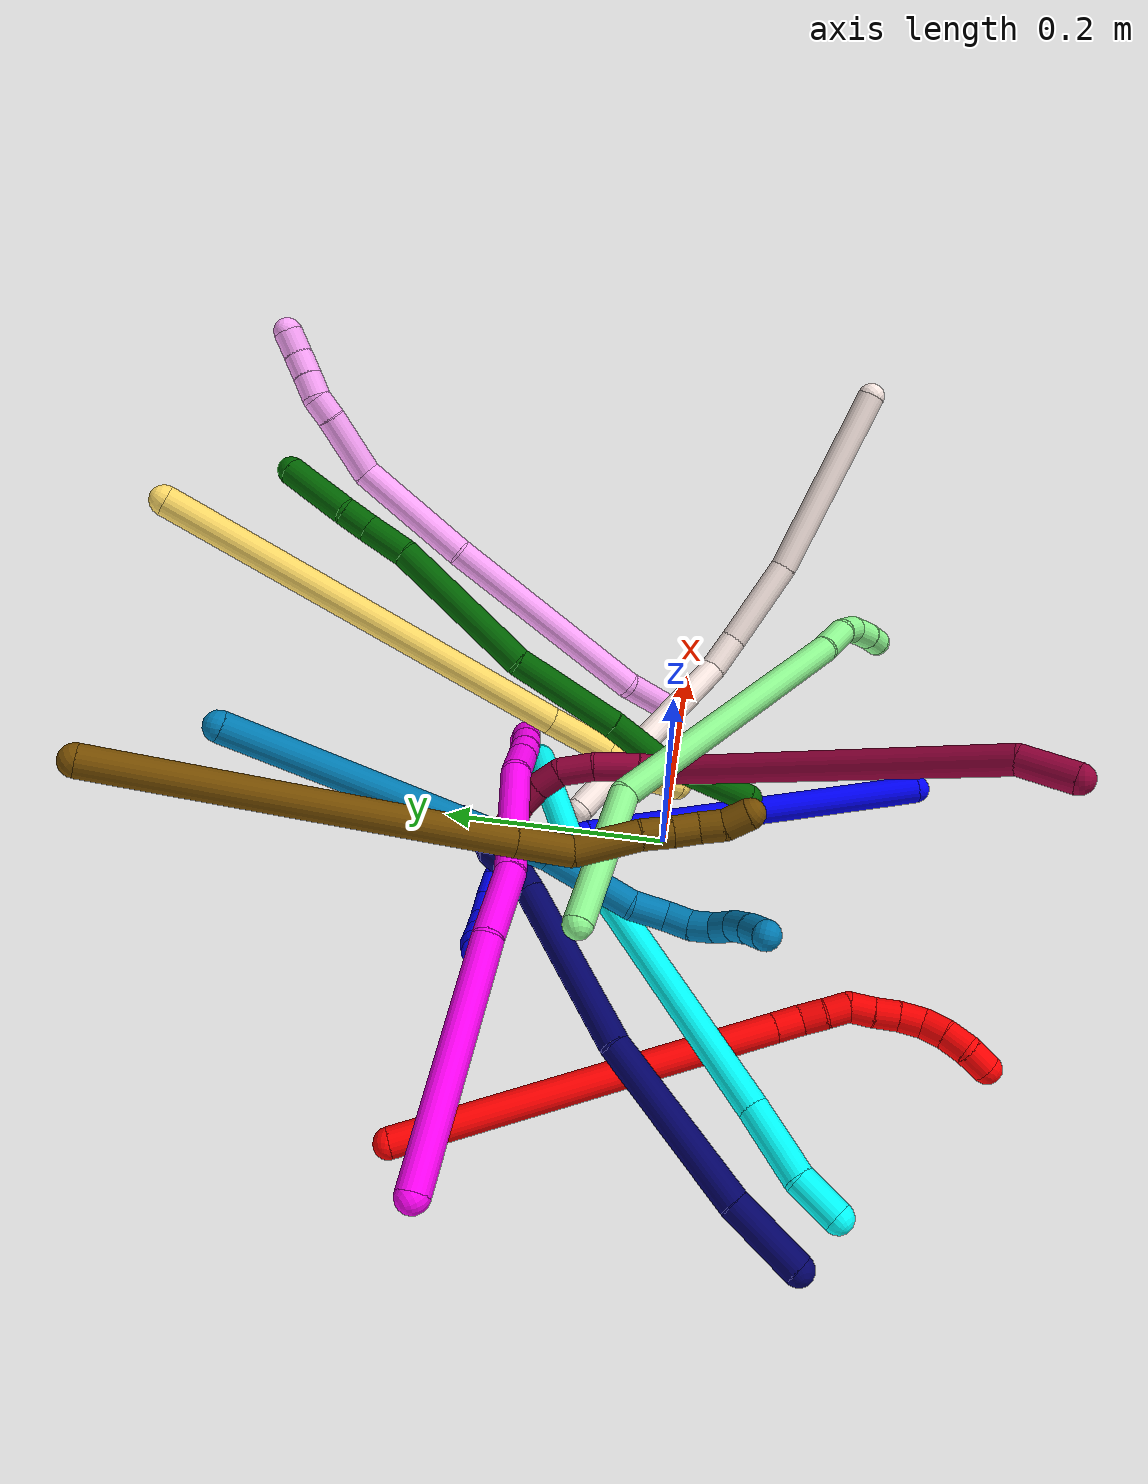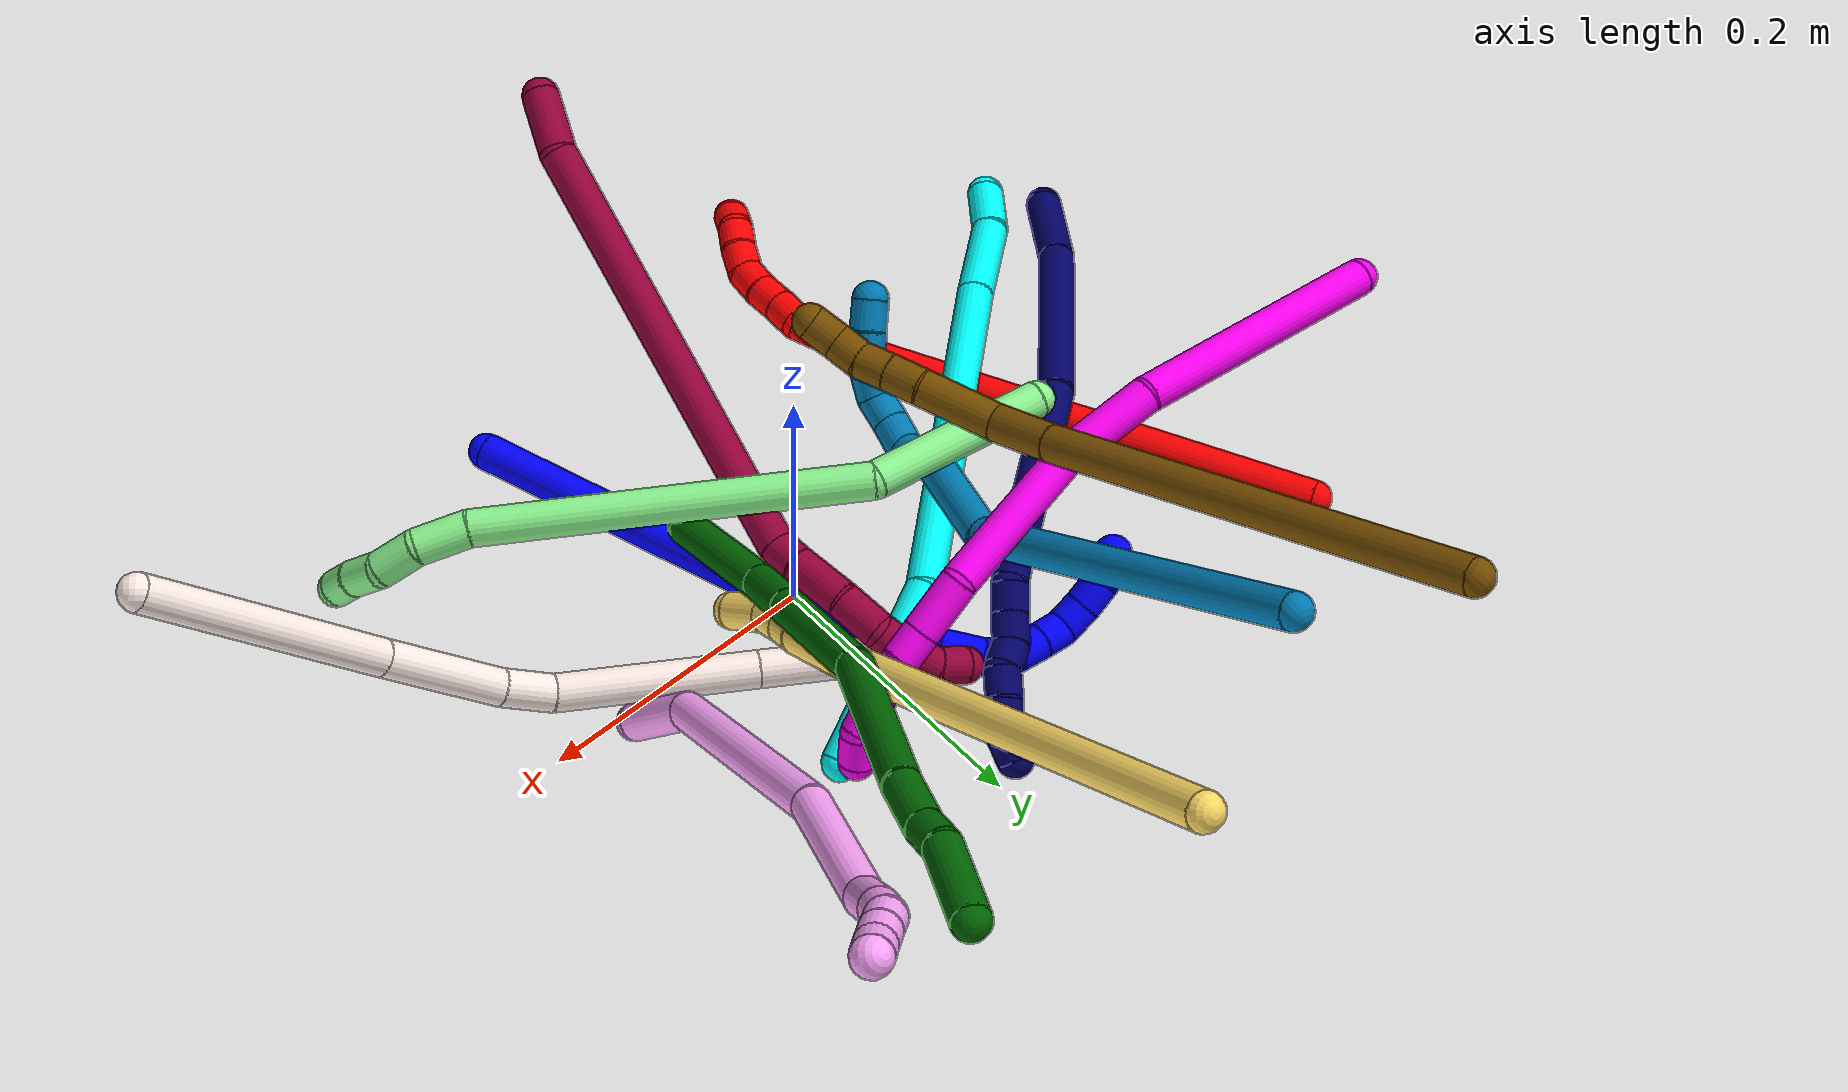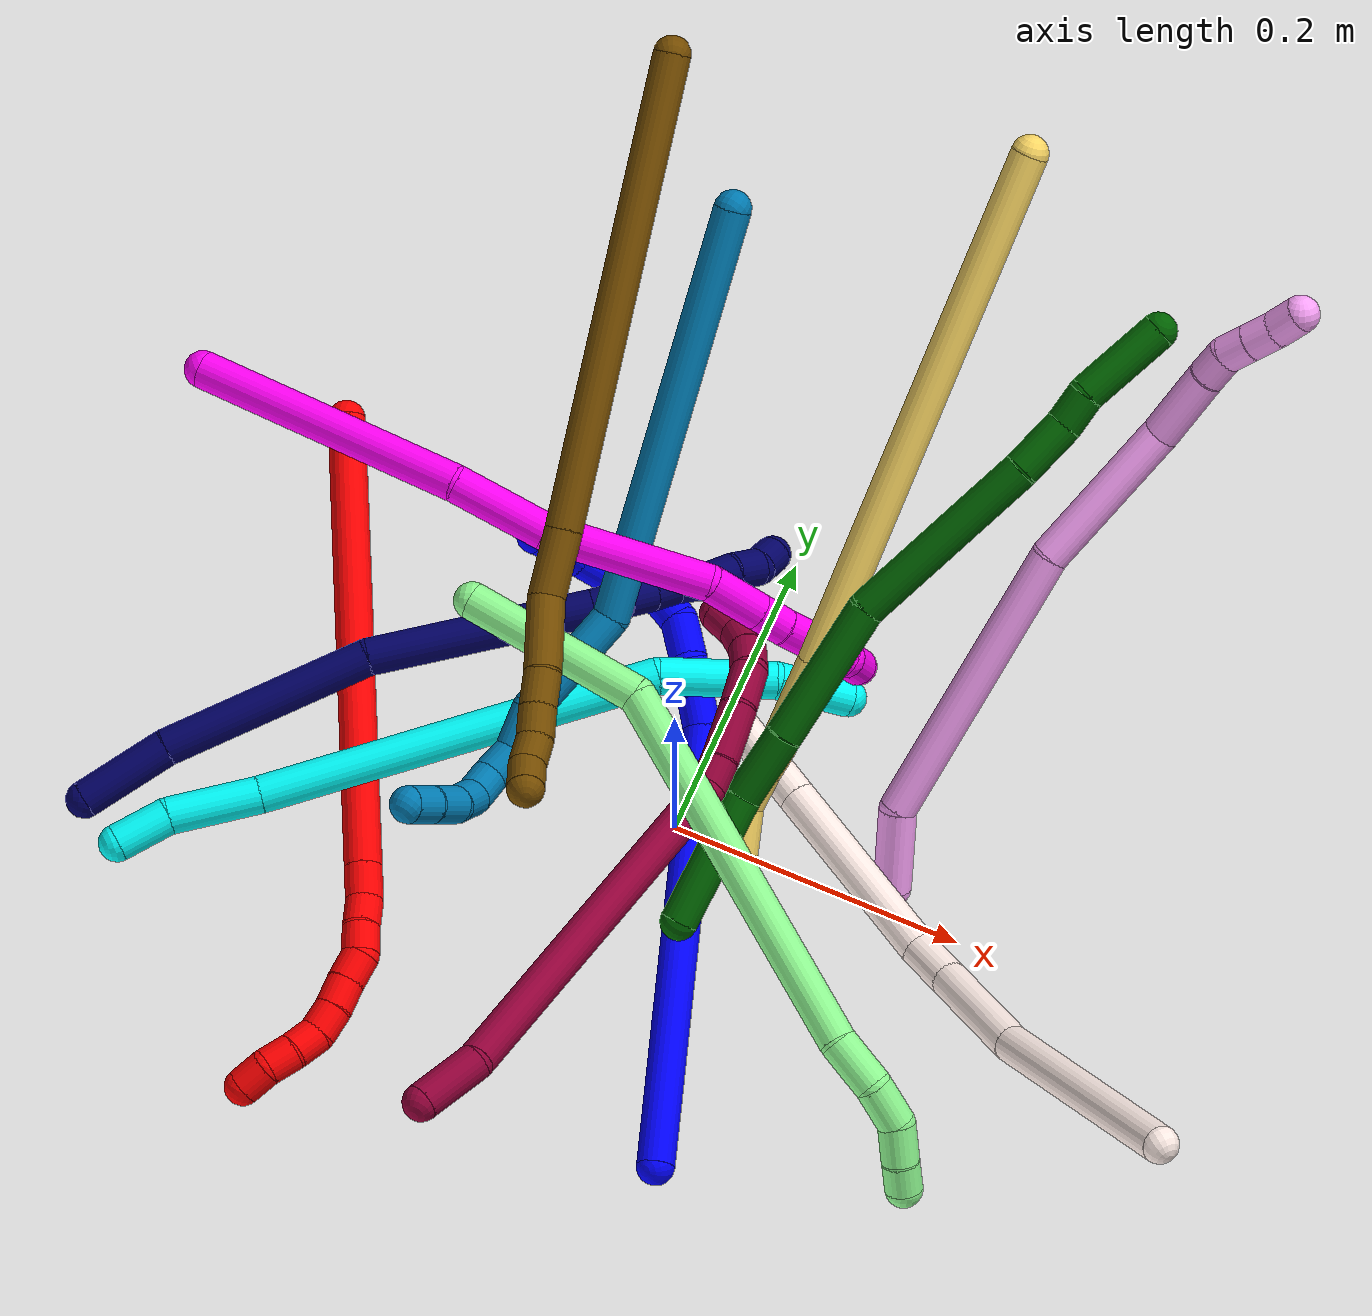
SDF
<sdf version="1.7">
 <world name="default">
  <plugin name="TubeGeneratorPlugin" filename="libtube_generator_plugin.so"/>
  <model name="photoneo_s_sensor">
   <static>1</static>
   <pose>0 0 2 1.57079 1.57079 3.14159</pose>
   <link name="link">
    <inertial><mass>0.1</mass></inertial>
    <sensor name="sensor" type="depth">
     <update_rate>30</update_rate>
     <camera>
      <horizontal_fov>1.22</horizontal_fov>
      <image><width>1920</width><height>1200</height><format>B8G8R8</format></image>
      <clip><near>0.1</near><far>4</far></clip>
      <depth_camera><output>points</output></depth_camera>
     </camera>
     <plugin name="camera_plugin" filename="libgazebo_ros_depth_camera.so">
      <baseline>0.2</baseline>
      <alwaysOn>1</alwaysOn>
      <updateRate>0.0</updateRate>
      <cameraName>camera_ir</cameraName>
      <imageTopicName>/camera/color/image_raw</imageTopicName>
      <cameraInfoTopicName>/camera/color/camera_info</cameraInfoTopicName>
      <depthImageTopicName>/camera/depth/image_raw</depthImageTopicName>
      <depthImageCameraInfoTopicName>/camera/depth/camera_info</depthImageCameraInfoTopicName>
      <pointCloudTopicName>/camera/depth/points</pointCloudTopicName>
      <frameName>fr_optical</frameName>
      <pointCloudCutoff>0.1</pointCloudCutoff>
      <pointCloudCutoffMax>2.0</pointCloudCutoffMax>
      <distortionK1>0</distortionK1>
      <distortionK2>0</distortionK2>
      <distortionK3>0</distortionK3>
      <distortionT1>0</distortionT1>
      <distortionT2>0</distortionT2>
      <CxPrime>0</CxPrime>
      <Cx>0</Cx>
      <Cy>0</Cy>
      <focalLength>0</focalLength>
      <hackBaseline>0</hackBaseline>
     </plugin>
    </sensor>
   </link>
  </model>
  <gravity>0 0 -9.8</gravity>
  <magnetic_field>6e-06 2.3e-05 -4.2e-05</magnetic_field>
  <atmosphere type="adiabatic"/>
  <physics name="default_physics" default="0" type="ode">
   <max_step_size>0.003</max_step_size>
   <real_time_factor>1</real_time_factor>
   <real_time_update_rate>1000</real_time_update_rate>
   <max_contacts>10000</max_contacts>
   <ode>
    <solver>
     <type>quick</type>
     <iters>100</iters>
     <sor>1.3</sor>
     <use_dynamic_moi_rescaling>0</use_dynamic_moi_rescaling>
    </solver>
    <constraints>
     <contact_max_correcting_vel>0</contact_max_correcting_vel>
     <contact_surface_layer>0.001</contact_surface_layer>
     <cfm>0</cfm>
     <erp>0.2</erp>
    </constraints>
   </ode>
  </physics>
  <scene><ambient>0.4 0.4 0.4 1</ambient><background>0.7 0.7 0.7 1</background><shadows>0</shadows></scene>
  <audio><device>default</device></audio>
  <spherical_coordinates>
   <surface_model>EARTH_WGS84</surface_model>
   <latitude_deg>0</latitude_deg>
   <longitude_deg>0</longitude_deg>
   <elevation>0</elevation>
   <heading_deg>0</heading_deg>
  </spherical_coordinates>
  <model name="bin">
   <static>1</static>
   <link name="bottom">
    <collision name="collision-bottom">
     <pose>0 0 -0.01 0 -0 0</pose>
     <geometry><box><size>0.8 0.6 0.02</size></box></geometry>
     <surface>
      <friction><ode><mu>100</mu><mu2>100</mu2></ode></friction>
      <contact><collide_bitmask>65535</collide_bitmask></contact>
     </surface>
    </collision>
   </link>
   <link name="west_wall">
    <collision name="collision-west_wall">
     <pose>-0.41 0 0.1 0 -0 0</pose>
     <geometry><box><size>0.02 0.6 0.2</size></box></geometry>
     <surface>
      <friction><ode><mu>100</mu><mu2>100</mu2></ode></friction>
      <contact><collide_bitmask>65535</collide_bitmask></contact>
     </surface>
    </collision>
   </link>
   <link name="east_wall">
    <collision name="collision-east_wall">
     <pose>0.41 0 0.1 0 -0 0</pose>
     <geometry><box><size>0.02 0.6 0.2</size></box></geometry>
     <surface>
      <friction><ode><mu>100</mu><mu2>100</mu2></ode></friction>
      <contact><collide_bitmask>65535</collide_bitmask></contact>
     </surface>
    </collision>
   </link>
   <link name="south_wall">
    <collision name="collision-south_wall">
     <pose>0 -0.31 0.1 0 -0 0</pose>
     <geometry><box><size>0.8 0.02 0.2</size></box></geometry>
     <surface>
      <friction><ode><mu>100</mu><mu2>100</mu2></ode></friction>
      <contact><collide_bitmask>65535</collide_bitmask></contact>
     </surface>
    </collision>
   </link>
   <link name="north_wall">
    <collision name="collision-north_wall">
     <pose>0 0.31 0.1 0 -0 0</pose>
     <geometry><box><size>0.8 0.02 0.2</size></box></geometry>
     <surface>
      <friction><ode><mu>100</mu><mu2>100</mu2></ode></friction>
      <contact><collide_bitmask>65535</collide_bitmask></contact>
     </surface>
    </collision>
   </link>
  </model>
  <model name="1">
   <static>0</static>
   <link name="1">
    <collision name="collision-cylinder-e_1_1_4">
     <pose>-0.035517 0.121609 -0.083028 -2.16985 -0.236684 0.442903</pose>
     <geometry><cylinder><radius>0.0125</radius><length>0.302945</length></cylinder></geometry>
     <surface>
      <friction><ode><mu>1.16</mu><mu2>1.16</mu2><slip1>0</slip1><slip2>0</slip2></ode></friction>
      <contact><ode><kp>1e+06</kp><kd>1</kd><max_vel>0</max_vel><min_depth>0.001</min_depth></ode></contact>
     </surface>
    </collision>
    <visual name="visual-cylinder-e_1_1_4">
     <pose>-0.035517 0.121609 -0.083028 -2.16985 -0.236684 0.442903</pose>
     <geometry><cylinder><radius>0.0125</radius><length>0.302945</length></cylinder></geometry>
     <material><ambient>0 0 1 1</ambient></material>
    </visual>
    <collision name="collision-cylinder-e_2_4_5">
     <pose>-0.075533 0.25246 -0.169364 -1.91444 -0.429658 0.600893</pose>
     <geometry><cylinder><radius>0.0125</radius><length>0.021595</length></cylinder></geometry>
     <surface>
      <friction><ode><mu>1.16</mu><mu2>1.16</mu2><slip1>0</slip1><slip2>0</slip2></ode></friction>
      <contact><ode><kp>1e+06</kp><kd>1</kd><max_vel>0</max_vel><min_depth>0.001</min_depth></ode></contact>
     </surface>
    </collision>
    <visual name="visual-cylinder-e_2_4_5">
     <pose>-0.075533 0.25246 -0.169364 -1.91444 -0.429658 0.600893</pose>
     <geometry><cylinder><radius>0.0125</radius><length>0.021595</length></cylinder></geometry>
     <material><ambient>0 0 1 1</ambient></material>
    </visual>
    <collision name="collision-cylinder-e_3_5_6">
     <pose>-0.084354 0.273664 -0.175131 -1.77361 -0.340303 0.415403</pose>
     <geometry><cylinder><radius>0.0125</radius><length>0.025909</length></cylinder></geometry>
     <surface>
      <friction><ode><mu>1.16</mu><mu2>1.16</mu2><slip1>0</slip1><slip2>0</slip2></ode></friction>
      <contact><ode><kp>1e+06</kp><kd>1</kd><max_vel>0</max_vel><min_depth>0.001</min_depth></ode></contact>
     </surface>
    </collision>
    <visual name="visual-cylinder-e_3_5_6">
     <pose>-0.084354 0.273664 -0.175131 -1.77361 -0.340303 0.415403</pose>
     <geometry><cylinder><radius>0.0125</radius><length>0.025909</length></cylinder></geometry>
     <material><ambient>0 0 1 1</ambient></material>
    </visual>
    <collision name="collision-cylinder-e_4_6_7">
     <pose>-0.095965 0.296572 -0.183271 -2.04942 -0.533676 0.845375</pose>
     <geometry><cylinder><radius>0.0125</radius><length>0.028649</length></cylinder></geometry>
     <surface>
      <friction><ode><mu>1.16</mu><mu2>1.16</mu2><slip1>0</slip1><slip2>0</slip2></ode></friction>
      <contact><ode><kp>1e+06</kp><kd>1</kd><max_vel>0</max_vel><min_depth>0.001</min_depth></ode></contact>
     </surface>
    </collision>
    <visual name="visual-cylinder-e_4_6_7">
     <pose>-0.095965 0.296572 -0.183271 -2.04942 -0.533676 0.845375</pose>
     <geometry><cylinder><radius>0.0125</radius><length>0.028649</length></cylinder></geometry>
     <material><ambient>0 0 1 1</ambient></material>
    </visual>
    <collision name="collision-cylinder-e_5_7_8">
     <pose>-0.111353 0.31344 -0.190656 -1.85125 -0.920506 1.16497</pose>
     <geometry><cylinder><radius>0.0125</radius><length>0.020357</length></cylinder></geometry>
     <surface>
      <friction><ode><mu>1.16</mu><mu2>1.16</mu2><slip1>0</slip1><slip2>0</slip2></ode></friction>
      <contact><ode><kp>1e+06</kp><kd>1</kd><max_vel>0</max_vel><min_depth>0.001</min_depth></ode></contact>
     </surface>
    </collision>
    <visual name="visual-cylinder-e_5_7_8">
     <pose>-0.111353 0.31344 -0.190656 -1.85125 -0.920506 1.16497</pose>
     <geometry><cylinder><radius>0.0125</radius><length>0.020357</length></cylinder></geometry>
     <material><ambient>0 0 1 1</ambient></material>
    </visual>
    <collision name="collision-cylinder-e_6_8_9">
     <pose>-0.128603 0.323142 -0.190203 -1.05191 -1.12662 0.702819</pose>
     <geometry><cylinder><radius>0.0125</radius><length>0.020264</length></cylinder></geometry>
     <surface>
      <friction><ode><mu>1.16</mu><mu2>1.16</mu2><slip1>0</slip1><slip2>0</slip2></ode></friction>
      <contact><ode><kp>1e+06</kp><kd>1</kd><max_vel>0</max_vel><min_depth>0.001</min_depth></ode></contact>
     </surface>
    </collision>
    <visual name="visual-cylinder-e_6_8_9">
     <pose>-0.128603 0.323142 -0.190203 -1.05191 -1.12662 0.702819</pose>
     <geometry><cylinder><radius>0.0125</radius><length>0.020264</length></cylinder></geometry>
     <material><ambient>0 0 1 1</ambient></material>
    </visual>
    <collision name="collision-cylinder-e_7_9_10">
     <pose>-0.146887 0.330428 -0.185575 -0.957135 -1.132 0.636792</pose>
     <geometry><cylinder><radius>0.0125</radius><length>0.020182</length></cylinder></geometry>
     <surface>
      <friction><ode><mu>1.16</mu><mu2>1.16</mu2><slip1>0</slip1><slip2>0</slip2></ode></friction>
      <contact><ode><kp>1e+06</kp><kd>1</kd><max_vel>0</max_vel><min_depth>0.001</min_depth></ode></contact>
     </surface>
    </collision>
    <visual name="visual-cylinder-e_7_9_10">
     <pose>-0.146887 0.330428 -0.185575 -0.957135 -1.132 0.636792</pose>
     <geometry><cylinder><radius>0.0125</radius><length>0.020182</length></cylinder></geometry>
     <material><ambient>0 0 1 1</ambient></material>
    </visual>
    <collision name="collision-cylinder-e_8_10_11">
     <pose>-0.162154 0.339398 -0.177384 -0.762458 -0.65929 0.272576</pose>
     <geometry><cylinder><radius>0.0125</radius><length>0.020023</length></cylinder></geometry>
     <surface>
      <friction><ode><mu>1.16</mu><mu2>1.16</mu2><slip1>0</slip1><slip2>0</slip2></ode></friction>
      <contact><ode><kp>1e+06</kp><kd>1</kd><max_vel>0</max_vel><min_depth>0.001</min_depth></ode></contact>
     </surface>
    </collision>
    <visual name="visual-cylinder-e_8_10_11">
     <pose>-0.162154 0.339398 -0.177384 -0.762458 -0.65929 0.272576</pose>
     <geometry><cylinder><radius>0.0125</radius><length>0.020023</length></cylinder></geometry>
     <material><ambient>0 0 1 1</ambient></material>
    </visual>
    <collision name="collision-cylinder-e_9_11_12">
     <pose>-0.172949 0.35081 -0.165053 -0.732743 -0.483042 0.188471</pose>
     <geometry><cylinder><radius>0.0125</radius><length>0.020076</length></cylinder></geometry>
     <surface>
      <friction><ode><mu>1.16</mu><mu2>1.16</mu2><slip1>0</slip1><slip2>0</slip2></ode></friction>
      <contact><ode><kp>1e+06</kp><kd>1</kd><max_vel>0</max_vel><min_depth>0.001</min_depth></ode></contact>
     </surface>
    </collision>
    <visual name="visual-cylinder-e_9_11_12">
     <pose>-0.172949 0.35081 -0.165053 -0.732743 -0.483042 0.188471</pose>
     <geometry><cylinder><radius>0.0125</radius><length>0.020076</length></cylinder></geometry>
     <material><ambient>0 0 1 1</ambient></material>
    </visual>
    <collision name="collision-cylinder-e_10_12_2">
     <pose>-0.180605 0.361271 -0.150039 -0.492873 -0.303936 0.077011</pose>
     <geometry><cylinder><radius>0.0125</radius><length>0.02</length></cylinder></geometry>
     <surface>
      <friction><ode><mu>1.16</mu><mu2>1.16</mu2><slip1>0</slip1><slip2>0</slip2></ode></friction>
      <contact><ode><kp>1e+06</kp><kd>1</kd><max_vel>0</max_vel><min_depth>0.001</min_depth></ode></contact>
     </surface>
    </collision>
    <visual name="visual-cylinder-e_10_12_2">
     <pose>-0.180605 0.361271 -0.150039 -0.492873 -0.303936 0.077011</pose>
     <geometry><cylinder><radius>0.0125</radius><length>0.02</length></cylinder></geometry>
     <material><ambient>0 0 1 1</ambient></material>
    </visual>
    <collision name="collision-sphere-2">
     <pose>-0.183597 0.365786 -0.141633 0 -0 0</pose>
     <geometry><sphere><radius>0.0125</radius></sphere></geometry>
     <surface>
      <friction><ode><mu>1.16</mu><mu2>1.16</mu2><slip1>0</slip1><slip2>0</slip2></ode></friction>
      <contact><ode><kp>1e+06</kp><kd>1</kd><max_vel>0</max_vel><min_depth>0.001</min_depth></ode></contact>
     </surface>
    </collision>
    <visual name="visual-sphere-2">
     <pose>-0.183597 0.365786 -0.141633 0 -0 0</pose>
     <geometry><sphere><radius>0.0125</radius></sphere></geometry>
     <material><ambient>0 0 1 1</ambient></material>
    </visual>
    <collision name="collision-sphere-12">
     <pose>-0.177612 0.356757 -0.158445 0 -0 0</pose>
     <geometry><sphere><radius>0.0125</radius></sphere></geometry>
     <surface>
      <friction><ode><mu>1.16</mu><mu2>1.16</mu2><slip1>0</slip1><slip2>0</slip2></ode></friction>
      <contact><ode><kp>1e+06</kp><kd>1</kd><max_vel>0</max_vel><min_depth>0.001</min_depth></ode></contact>
     </surface>
    </collision>
    <visual name="visual-sphere-12">
     <pose>-0.177612 0.356757 -0.158445 0 -0 0</pose>
     <geometry><sphere><radius>0.0125</radius></sphere></geometry>
     <material><ambient>0 0 1 1</ambient></material>
    </visual>
    <collision name="collision-sphere-11">
     <pose>-0.168287 0.344864 -0.171661 0 -0 0</pose>
     <geometry><sphere><radius>0.0125</radius></sphere></geometry>
     <surface>
      <friction><ode><mu>1.16</mu><mu2>1.16</mu2><slip1>0</slip1><slip2>0</slip2></ode></friction>
      <contact><ode><kp>1e+06</kp><kd>1</kd><max_vel>0</max_vel><min_depth>0.001</min_depth></ode></contact>
     </surface>
    </collision>
    <visual name="visual-sphere-11">
     <pose>-0.168287 0.344864 -0.171661 0 -0 0</pose>
     <geometry><sphere><radius>0.0125</radius></sphere></geometry>
     <material><ambient>0 0 1 1</ambient></material>
    </visual>
    <collision name="collision-sphere-10">
     <pose>-0.156022 0.333933 -0.183106 0 -0 0</pose>
     <geometry><sphere><radius>0.0125</radius></sphere></geometry>
     <surface>
      <friction><ode><mu>1.16</mu><mu2>1.16</mu2><slip1>0</slip1><slip2>0</slip2></ode></friction>
      <contact><ode><kp>1e+06</kp><kd>1</kd><max_vel>0</max_vel><min_depth>0.001</min_depth></ode></contact>
     </surface>
    </collision>
    <visual name="visual-sphere-10">
     <pose>-0.156022 0.333933 -0.183106 0 -0 0</pose>
     <geometry><sphere><radius>0.0125</radius></sphere></geometry>
     <material><ambient>0 0 1 1</ambient></material>
    </visual>
    <collision name="collision-sphere-9">
     <pose>-0.137752 0.326923 -0.188044 0 -0 0</pose>
     <geometry><sphere><radius>0.0125</radius></sphere></geometry>
     <surface>
      <friction><ode><mu>1.16</mu><mu2>1.16</mu2><slip1>0</slip1><slip2>0</slip2></ode></friction>
      <contact><ode><kp>1e+06</kp><kd>1</kd><max_vel>0</max_vel><min_depth>0.001</min_depth></ode></contact>
     </surface>
    </collision>
    <visual name="visual-sphere-9">
     <pose>-0.137752 0.326923 -0.188044 0 -0 0</pose>
     <geometry><sphere><radius>0.0125</radius></sphere></geometry>
     <material><ambient>0 0 1 1</ambient></material>
    </visual>
    <collision name="collision-sphere-4">
     <pose>-0.071035 0.243218 -0.166057 0 -0 0</pose>
     <geometry><sphere><radius>0.0125</radius></sphere></geometry>
     <surface>
      <friction><ode><mu>1.16</mu><mu2>1.16</mu2><slip1>0</slip1><slip2>0</slip2></ode></friction>
      <contact><ode><kp>1e+06</kp><kd>1</kd><max_vel>0</max_vel><min_depth>0.001</min_depth></ode></contact>
     </surface>
    </collision>
    <visual name="visual-sphere-4">
     <pose>-0.071035 0.243218 -0.166057 0 -0 0</pose>
     <geometry><sphere><radius>0.0125</radius></sphere></geometry>
     <material><ambient>0 0 1 1</ambient></material>
    </visual>
    <collision name="collision-sphere-1">
     <geometry><sphere><radius>0.0125</radius></sphere></geometry>
     <surface>
      <friction><ode><mu>1.16</mu><mu2>1.16</mu2><slip1>0</slip1><slip2>0</slip2></ode></friction>
      <contact><ode><kp>1e+06</kp><kd>1</kd><max_vel>0</max_vel><min_depth>0.001</min_depth></ode></contact>
     </surface>
    </collision>
    <visual name="visual-sphere-1">
     <geometry><sphere><radius>0.0125</radius></sphere></geometry>
     <material><ambient>0 0 1 1</ambient></material>
    </visual>
    <collision name="collision-sphere-8">
     <pose>-0.119454 0.319361 -0.192362 0 -0 0</pose>
     <geometry><sphere><radius>0.0125</radius></sphere></geometry>
     <surface>
      <friction><ode><mu>1.16</mu><mu2>1.16</mu2><slip1>0</slip1><slip2>0</slip2></ode></friction>
      <contact><ode><kp>1e+06</kp><kd>1</kd><max_vel>0</max_vel><min_depth>0.001</min_depth></ode></contact>
     </surface>
    </collision>
    <visual name="visual-sphere-8">
     <pose>-0.119454 0.319361 -0.192362 0 -0 0</pose>
     <geometry><sphere><radius>0.0125</radius></sphere></geometry>
     <material><ambient>0 0 1 1</ambient></material>
    </visual>
    <collision name="collision-sphere-5">
     <pose>-0.08003 0.261702 -0.172671 0 -0 0</pose>
     <geometry><sphere><radius>0.0125</radius></sphere></geometry>
     <surface>
      <friction><ode><mu>1.16</mu><mu2>1.16</mu2><slip1>0</slip1><slip2>0</slip2></ode></friction>
      <contact><ode><kp>1e+06</kp><kd>1</kd><max_vel>0</max_vel><min_depth>0.001</min_depth></ode></contact>
     </surface>
    </collision>
    <visual name="visual-sphere-5">
     <pose>-0.08003 0.261702 -0.172671 0 -0 0</pose>
     <geometry><sphere><radius>0.0125</radius></sphere></geometry>
     <material><ambient>0 0 1 1</ambient></material>
    </visual>
    <collision name="collision-sphere-6">
     <pose>-0.088678 0.285625 -0.177591 0 -0 0</pose>
     <geometry><sphere><radius>0.0125</radius></sphere></geometry>
     <surface>
      <friction><ode><mu>1.16</mu><mu2>1.16</mu2><slip1>0</slip1><slip2>0</slip2></ode></friction>
      <contact><ode><kp>1e+06</kp><kd>1</kd><max_vel>0</max_vel><min_depth>0.001</min_depth></ode></contact>
     </surface>
    </collision>
    <visual name="visual-sphere-6">
     <pose>-0.088678 0.285625 -0.177591 0 -0 0</pose>
     <geometry><sphere><radius>0.0125</radius></sphere></geometry>
     <material><ambient>0 0 1 1</ambient></material>
    </visual>
    <collision name="collision-sphere-7">
     <pose>-0.103252 0.307518 -0.188951 0 -0 0</pose>
     <geometry><sphere><radius>0.0125</radius></sphere></geometry>
     <surface>
      <friction><ode><mu>1.16</mu><mu2>1.16</mu2><slip1>0</slip1><slip2>0</slip2></ode></friction>
      <contact><ode><kp>1e+06</kp><kd>1</kd><max_vel>0</max_vel><min_depth>0.001</min_depth></ode></contact>
     </surface>
    </collision>
    <visual name="visual-sphere-7">
     <pose>-0.103252 0.307518 -0.188951 0 -0 0</pose>
     <geometry><sphere><radius>0.0125</radius></sphere></geometry>
     <material><ambient>0 0 1 1</ambient></material>
    </visual>
    <inertial>
     <pose>-0.070988 0.197082 -0.119891 0 -0 0</pose>
     <mass>0.5</mass>
     <inertia>
      <ixx>0.003018</ixx>
      <ixy>0</ixy>
      <ixz>0</ixz>
      <iyy>1.9e-05</iyy>
      <iyz>0</iyz>
      <izz>-0.001336</izz>
     </inertia>
    </inertial>
   </link>
   <pose>0.083026 -0.222425 0.013651 0.721413 -0.495531 0.043967</pose>
  </model>
  <model name="2">
   <static>0</static>
   <link name="2">
    <collision name="collision-cylinder-e_1_1_4">
     <pose>0.105596 -0.094481 0.069519 0.936448 0.732934 0.383437</pose>
     <geometry><cylinder><radius>0.0125</radius><length>0.315658</length></cylinder></geometry>
     <surface>
      <friction><ode><mu>1.16</mu><mu2>1.16</mu2><slip1>0</slip1><slip2>0</slip2></ode></friction>
      <contact><ode><kp>1e+06</kp><kd>1</kd><max_vel>0</max_vel><min_depth>0.001</min_depth></ode></contact>
     </surface>
    </collision>
    <visual name="visual-cylinder-e_1_1_4">
     <pose>0.105596 -0.094481 0.069519 0.936448 0.732934 0.383437</pose>
     <geometry><cylinder><radius>0.0125</radius><length>0.315658</length></cylinder></geometry>
     <material><ambient>1 0 0 1</ambient></material>
    </visual>
    <collision name="collision-cylinder-e_2_4_5">
     <pose>0.219106 -0.196065 0.144253 0.937448 0.73174 0.383234</pose>
     <geometry><cylinder><radius>0.0125</radius><length>0.023687</length></cylinder></geometry>
     <surface>
      <friction><ode><mu>1.16</mu><mu2>1.16</mu2><slip1>0</slip1><slip2>0</slip2></ode></friction>
      <contact><ode><kp>1e+06</kp><kd>1</kd><max_vel>0</max_vel><min_depth>0.001</min_depth></ode></contact>
     </surface>
    </collision>
    <visual name="visual-cylinder-e_2_4_5">
     <pose>0.219106 -0.196065 0.144253 0.937448 0.73174 0.383234</pose>
     <geometry><cylinder><radius>0.0125</radius><length>0.023687</length></cylinder></geometry>
     <material><ambient>1 0 0 1</ambient></material>
    </visual>
    <collision name="collision-cylinder-e_3_5_6">
     <pose>0.232955 -0.211149 0.152114 1.25072 0.614729 0.450598</pose>
     <geometry><cylinder><radius>0.0125</radius><length>0.020586</length></cylinder></geometry>
     <surface>
      <friction><ode><mu>1.16</mu><mu2>1.16</mu2><slip1>0</slip1><slip2>0</slip2></ode></friction>
      <contact><ode><kp>1e+06</kp><kd>1</kd><max_vel>0</max_vel><min_depth>0.001</min_depth></ode></contact>
     </surface>
    </collision>
    <visual name="visual-cylinder-e_3_5_6">
     <pose>0.232955 -0.211149 0.152114 1.25072 0.614729 0.450598</pose>
     <geometry><cylinder><radius>0.0125</radius><length>0.020586</length></cylinder></geometry>
     <material><ambient>1 0 0 1</ambient></material>
    </visual>
    <collision name="collision-cylinder-e_4_6_7">
     <pose>0.245224 -0.225927 0.158471 1.07098 0.685409 0.417208</pose>
     <geometry><cylinder><radius>0.0125</radius><length>0.020006</length></cylinder></geometry>
     <surface>
      <friction><ode><mu>1.16</mu><mu2>1.16</mu2><slip1>0</slip1><slip2>0</slip2></ode></friction>
      <contact><ode><kp>1e+06</kp><kd>1</kd><max_vel>0</max_vel><min_depth>0.001</min_depth></ode></contact>
     </surface>
    </collision>
    <visual name="visual-cylinder-e_4_6_7">
     <pose>0.245224 -0.225927 0.158471 1.07098 0.685409 0.417208</pose>
     <geometry><cylinder><radius>0.0125</radius><length>0.020006</length></cylinder></geometry>
     <material><ambient>1 0 0 1</ambient></material>
    </visual>
    <collision name="collision-cylinder-e_5_7_8">
     <pose>0.260047 -0.237997 0.161651 1.67122 1.01284 1.10037</pose>
     <geometry><cylinder><radius>0.0125</radius><length>0.020021</length></cylinder></geometry>
     <surface>
      <friction><ode><mu>1.16</mu><mu2>1.16</mu2><slip1>0</slip1><slip2>0</slip2></ode></friction>
      <contact><ode><kp>1e+06</kp><kd>1</kd><max_vel>0</max_vel><min_depth>0.001</min_depth></ode></contact>
     </surface>
    </collision>
    <visual name="visual-cylinder-e_5_7_8">
     <pose>0.260047 -0.237997 0.161651 1.67122 1.01284 1.10037</pose>
     <geometry><cylinder><radius>0.0125</radius><length>0.020021</length></cylinder></geometry>
     <material><ambient>1 0 0 1</ambient></material>
    </visual>
    <collision name="collision-cylinder-e_6_8_9">
     <pose>0.276862 -0.24883 0.161363 1.52696 0.981475 0.945466</pose>
     <geometry><cylinder><radius>0.0125</radius><length>0.020024</length></cylinder></geometry>
     <surface>
      <friction><ode><mu>1.16</mu><mu2>1.16</mu2><slip1>0</slip1><slip2>0</slip2></ode></friction>
      <contact><ode><kp>1e+06</kp><kd>1</kd><max_vel>0</max_vel><min_depth>0.001</min_depth></ode></contact>
     </surface>
    </collision>
    <visual name="visual-cylinder-e_6_8_9">
     <pose>0.276862 -0.24883 0.161363 1.52696 0.981475 0.945466</pose>
     <geometry><cylinder><radius>0.0125</radius><length>0.020024</length></cylinder></geometry>
     <material><ambient>1 0 0 1</ambient></material>
    </visual>
    <collision name="collision-cylinder-e_7_9_10">
     <pose>0.293623 -0.259632 0.160437 1.79033 1.00383 1.20081</pose>
     <geometry><cylinder><radius>0.0125</radius><length>0.020005</length></cylinder></geometry>
     <surface>
      <friction><ode><mu>1.16</mu><mu2>1.16</mu2><slip1>0</slip1><slip2>0</slip2></ode></friction>
      <contact><ode><kp>1e+06</kp><kd>1</kd><max_vel>0</max_vel><min_depth>0.001</min_depth></ode></contact>
     </surface>
    </collision>
    <visual name="visual-cylinder-e_7_9_10">
     <pose>0.293623 -0.259632 0.160437 1.79033 1.00383 1.20081</pose>
     <geometry><cylinder><radius>0.0125</radius><length>0.020005</length></cylinder></geometry>
     <material><ambient>1 0 0 1</ambient></material>
    </visual>
    <collision name="collision-cylinder-e_8_10_11">
     <pose>0.309182 -0.270284 0.15479 2.26226 0.792516 1.45395</pose>
     <geometry><cylinder><radius>0.0125</radius><length>0.020002</length></cylinder></geometry>
     <surface>
      <friction><ode><mu>1.16</mu><mu2>1.16</mu2><slip1>0</slip1><slip2>0</slip2></ode></friction>
      <contact><ode><kp>1e+06</kp><kd>1</kd><max_vel>0</max_vel><min_depth>0.001</min_depth></ode></contact>
     </surface>
    </collision>
    <visual name="visual-cylinder-e_8_10_11">
     <pose>0.309182 -0.270284 0.15479 2.26226 0.792516 1.45395</pose>
     <geometry><cylinder><radius>0.0125</radius><length>0.020002</length></cylinder></geometry>
     <material><ambient>1 0 0 1</ambient></material>
    </visual>
    <collision name="collision-cylinder-e_9_11_12">
     <pose>0.323806 -0.279605 0.144978 2.50871 0.848093 1.88653</pose>
     <geometry><cylinder><radius>0.0125</radius><length>0.020005</length></cylinder></geometry>
     <surface>
      <friction><ode><mu>1.16</mu><mu2>1.16</mu2><slip1>0</slip1><slip2>0</slip2></ode></friction>
      <contact><ode><kp>1e+06</kp><kd>1</kd><max_vel>0</max_vel><min_depth>0.001</min_depth></ode></contact>
     </surface>
    </collision>
    <visual name="visual-cylinder-e_9_11_12">
     <pose>0.323806 -0.279605 0.144978 2.50871 0.848093 1.88653</pose>
     <geometry><cylinder><radius>0.0125</radius><length>0.020005</length></cylinder></geometry>
     <material><ambient>1 0 0 1</ambient></material>
    </visual>
    <collision name="collision-cylinder-e_10_12_2">
     <pose>0.340541 -0.284347 0.135885 2.92455 1.17576 2.81753</pose>
     <geometry><cylinder><radius>0.0125</radius><length>0.020006</length></cylinder></geometry>
     <surface>
      <friction><ode><mu>1.16</mu><mu2>1.16</mu2><slip1>0</slip1><slip2>0</slip2></ode></friction>
      <contact><ode><kp>1e+06</kp><kd>1</kd><max_vel>0</max_vel><min_depth>0.001</min_depth></ode></contact>
     </surface>
    </collision>
    <visual name="visual-cylinder-e_10_12_2">
     <pose>0.340541 -0.284347 0.135885 2.92455 1.17576 2.81753</pose>
     <geometry><cylinder><radius>0.0125</radius><length>0.020006</length></cylinder></geometry>
     <material><ambient>1 0 0 1</ambient></material>
    </visual>
    <collision name="collision-sphere-2">
     <pose>0.349774 -0.285176 0.132125 0 -0 0</pose>
     <geometry><sphere><radius>0.0125</radius></sphere></geometry>
     <surface>
      <friction><ode><mu>1.16</mu><mu2>1.16</mu2><slip1>0</slip1><slip2>0</slip2></ode></friction>
      <contact><ode><kp>1e+06</kp><kd>1</kd><max_vel>0</max_vel><min_depth>0.001</min_depth></ode></contact>
     </surface>
    </collision>
    <visual name="visual-sphere-2">
     <pose>0.349774 -0.285176 0.132125 0 -0 0</pose>
     <geometry><sphere><radius>0.0125</radius></sphere></geometry>
     <material><ambient>1 0 0 1</ambient></material>
    </visual>
    <collision name="collision-sphere-12">
     <pose>0.331308 -0.283518 0.139644 0 -0 0</pose>
     <geometry><sphere><radius>0.0125</radius></sphere></geometry>
     <surface>
      <friction><ode><mu>1.16</mu><mu2>1.16</mu2><slip1>0</slip1><slip2>0</slip2></ode></friction>
      <contact><ode><kp>1e+06</kp><kd>1</kd><max_vel>0</max_vel><min_depth>0.001</min_depth></ode></contact>
     </surface>
    </collision>
    <visual name="visual-sphere-12">
     <pose>0.331308 -0.283518 0.139644 0 -0 0</pose>
     <geometry><sphere><radius>0.0125</radius></sphere></geometry>
     <material><ambient>1 0 0 1</ambient></material>
    </visual>
    <collision name="collision-sphere-11">
     <pose>0.316304 -0.275692 0.150313 0 -0 0</pose>
     <geometry><sphere><radius>0.0125</radius></sphere></geometry>
     <surface>
      <friction><ode><mu>1.16</mu><mu2>1.16</mu2><slip1>0</slip1><slip2>0</slip2></ode></friction>
      <contact><ode><kp>1e+06</kp><kd>1</kd><max_vel>0</max_vel><min_depth>0.001</min_depth></ode></contact>
     </surface>
    </collision>
    <visual name="visual-sphere-11">
     <pose>0.316304 -0.275692 0.150313 0 -0 0</pose>
     <geometry><sphere><radius>0.0125</radius></sphere></geometry>
     <material><ambient>1 0 0 1</ambient></material>
    </visual>
    <collision name="collision-sphere-10">
     <pose>0.30206 -0.264875 0.159267 0 -0 0</pose>
     <geometry><sphere><radius>0.0125</radius></sphere></geometry>
     <surface>
      <friction><ode><mu>1.16</mu><mu2>1.16</mu2><slip1>0</slip1><slip2>0</slip2></ode></friction>
      <contact><ode><kp>1e+06</kp><kd>1</kd><max_vel>0</max_vel><min_depth>0.001</min_depth></ode></contact>
     </surface>
    </collision>
    <visual name="visual-sphere-10">
     <pose>0.30206 -0.264875 0.159267 0 -0 0</pose>
     <geometry><sphere><radius>0.0125</radius></sphere></geometry>
     <material><ambient>1 0 0 1</ambient></material>
    </visual>
    <collision name="collision-sphere-9">
     <pose>0.285185 -0.254389 0.161607 0 -0 0</pose>
     <geometry><sphere><radius>0.0125</radius></sphere></geometry>
     <surface>
      <friction><ode><mu>1.16</mu><mu2>1.16</mu2><slip1>0</slip1><slip2>0</slip2></ode></friction>
      <contact><ode><kp>1e+06</kp><kd>1</kd><max_vel>0</max_vel><min_depth>0.001</min_depth></ode></contact>
     </surface>
    </collision>
    <visual name="visual-sphere-9">
     <pose>0.285185 -0.254389 0.161607 0 -0 0</pose>
     <geometry><sphere><radius>0.0125</radius></sphere></geometry>
     <material><ambient>1 0 0 1</ambient></material>
    </visual>
    <collision name="collision-sphere-4">
     <pose>0.211192 -0.188962 0.139037 0 -0 0</pose>
     <geometry><sphere><radius>0.0125</radius></sphere></geometry>
     <surface>
      <friction><ode><mu>1.16</mu><mu2>1.16</mu2><slip1>0</slip1><slip2>0</slip2></ode></friction>
      <contact><ode><kp>1e+06</kp><kd>1</kd><max_vel>0</max_vel><min_depth>0.001</min_depth></ode></contact>
     </surface>
    </collision>
    <visual name="visual-sphere-4">
     <pose>0.211192 -0.188962 0.139037 0 -0 0</pose>
     <geometry><sphere><radius>0.0125</radius></sphere></geometry>
     <material><ambient>1 0 0 1</ambient></material>
    </visual>
    <collision name="collision-sphere-1">
     <geometry><sphere><radius>0.0125</radius></sphere></geometry>
     <surface>
      <friction><ode><mu>1.16</mu><mu2>1.16</mu2><slip1>0</slip1><slip2>0</slip2></ode></friction>
      <contact><ode><kp>1e+06</kp><kd>1</kd><max_vel>0</max_vel><min_depth>0.001</min_depth></ode></contact>
     </surface>
    </collision>
    <visual name="visual-sphere-1">
     <geometry><sphere><radius>0.0125</radius></sphere></geometry>
     <material><ambient>1 0 0 1</ambient></material>
    </visual>
    <collision name="collision-sphere-8">
     <pose>0.26854 -0.243271 0.161119 0 -0 0</pose>
     <geometry><sphere><radius>0.0125</radius></sphere></geometry>
     <surface>
      <friction><ode><mu>1.16</mu><mu2>1.16</mu2><slip1>0</slip1><slip2>0</slip2></ode></friction>
      <contact><ode><kp>1e+06</kp><kd>1</kd><max_vel>0</max_vel><min_depth>0.001</min_depth></ode></contact>
     </surface>
    </collision>
    <visual name="visual-sphere-8">
     <pose>0.26854 -0.243271 0.161119 0 -0 0</pose>
     <geometry><sphere><radius>0.0125</radius></sphere></geometry>
     <material><ambient>1 0 0 1</ambient></material>
    </visual>
    <collision name="collision-sphere-5">
     <pose>0.227019 -0.203168 0.149468 0 -0 0</pose>
     <geometry><sphere><radius>0.0125</radius></sphere></geometry>
     <surface>
      <friction><ode><mu>1.16</mu><mu2>1.16</mu2><slip1>0</slip1><slip2>0</slip2></ode></friction>
      <contact><ode><kp>1e+06</kp><kd>1</kd><max_vel>0</max_vel><min_depth>0.001</min_depth></ode></contact>
     </surface>
    </collision>
    <visual name="visual-sphere-5">
     <pose>0.227019 -0.203168 0.149468 0 -0 0</pose>
     <geometry><sphere><radius>0.0125</radius></sphere></geometry>
     <material><ambient>1 0 0 1</ambient></material>
    </visual>
    <collision name="collision-sphere-6">
     <pose>0.238892 -0.219131 0.154759 0 -0 0</pose>
     <geometry><sphere><radius>0.0125</radius></sphere></geometry>
     <surface>
      <friction><ode><mu>1.16</mu><mu2>1.16</mu2><slip1>0</slip1><slip2>0</slip2></ode></friction>
      <contact><ode><kp>1e+06</kp><kd>1</kd><max_vel>0</max_vel><min_depth>0.001</min_depth></ode></contact>
     </surface>
    </collision>
    <visual name="visual-sphere-6">
     <pose>0.238892 -0.219131 0.154759 0 -0 0</pose>
     <geometry><sphere><radius>0.0125</radius></sphere></geometry>
     <material><ambient>1 0 0 1</ambient></material>
    </visual>
    <collision name="collision-sphere-7">
     <pose>0.251555 -0.232724 0.162182 0 -0 0</pose>
     <geometry><sphere><radius>0.0125</radius></sphere></geometry>
     <surface>
      <friction><ode><mu>1.16</mu><mu2>1.16</mu2><slip1>0</slip1><slip2>0</slip2></ode></friction>
      <contact><ode><kp>1e+06</kp><kd>1</kd><max_vel>0</max_vel><min_depth>0.001</min_depth></ode></contact>
     </surface>
    </collision>
    <visual name="visual-sphere-7">
     <pose>0.251555 -0.232724 0.162182 0 -0 0</pose>
     <geometry><sphere><radius>0.0125</radius></sphere></geometry>
     <material><ambient>1 0 0 1</ambient></material>
    </visual>
    <inertial>
     <pose>0.168646 -0.149929 0.10011 0 -0 0</pose>
     <mass>0.5</mass>
     <inertia>
      <ixx>0.002584</ixx>
      <ixy>0</ixy>
      <ixz>0</ixz>
      <iyy>0.002703</iyy>
      <iyz>0</iyz>
      <izz>-0.000178</izz>
     </inertia>
    </inertial>
   </link>
   <pose>-0.3125 0.173926 0.011497 -1.84884 0.596967 -1.74373</pose>
  </model>
  <model name="3">
   <static>0</static>
   <link name="3">
    <collision name="collision-cylinder-e_1_1_4">
     <pose>-0.002304 0.00022 -0.018431 -3.12967 -0.124345 2.95057</pose>
     <geometry><cylinder><radius>0.0125</radius><length>0.037152</length></cylinder></geometry>
     <surface>
      <friction><ode><mu>1.16</mu><mu2>1.16</mu2><slip1>0</slip1><slip2>0</slip2></ode></friction>
      <contact><ode><kp>1e+06</kp><kd>1</kd><max_vel>0</max_vel><min_depth>0.001</min_depth></ode></contact>
     </surface>
    </collision>
    <visual name="visual-cylinder-e_1_1_4">
     <pose>-0.002304 0.00022 -0.018431 -3.12967 -0.124345 2.95057</pose>
     <geometry><cylinder><radius>0.0125</radius><length>0.037152</length></cylinder></geometry>
     <material><ambient>0.003922 1 0.996078 1</ambient></material>
    </visual>
    <collision name="collision-cylinder-e_2_4_5">
     <pose>-0.000643 0.003036 -0.06728 -3.05643 0.129158 -1.97645</pose>
     <geometry><cylinder><radius>0.0125</radius><length>0.06157</length></cylinder></geometry>
     <surface>
      <friction><ode><mu>1.16</mu><mu2>1.16</mu2><slip1>0</slip1><slip2>0</slip2></ode></friction>
      <contact><ode><kp>1e+06</kp><kd>1</kd><max_vel>0</max_vel><min_depth>0.001</min_depth></ode></contact>
     </surface>
    </collision>
    <visual name="visual-cylinder-e_2_4_5">
     <pose>-0.000643 0.003036 -0.06728 -3.05643 0.129158 -1.97645</pose>
     <geometry><cylinder><radius>0.0125</radius><length>0.06157</length></cylinder></geometry>
     <material><ambient>0.003922 1 0.996078 1</ambient></material>
    </visual>
    <collision name="collision-cylinder-e_3_5_6">
     <pose>0.011475 0.020175 -0.231817 -3.03359 0.060359 -1.01866</pose>
     <geometry><cylinder><radius>0.0125</radius><length>0.270301</length></cylinder></geometry>
     <surface>
      <friction><ode><mu>1.16</mu><mu2>1.16</mu2><slip1>0</slip1><slip2>0</slip2></ode></friction>
      <contact><ode><kp>1e+06</kp><kd>1</kd><max_vel>0</max_vel><min_depth>0.001</min_depth></ode></contact>
     </surface>
    </collision>
    <visual name="visual-cylinder-e_3_5_6">
     <pose>0.011475 0.020175 -0.231817 -3.03359 0.060359 -1.01866</pose>
     <geometry><cylinder><radius>0.0125</radius><length>0.270301</length></cylinder></geometry>
     <material><ambient>0.003922 1 0.996078 1</ambient></material>
    </visual>
    <collision name="collision-cylinder-e_4_6_7">
     <pose>0.034666 0.037535 -0.401695 -3.06296 0.396975 -2.75534</pose>
     <geometry><cylinder><radius>0.0125</radius><length>0.077792</length></cylinder></geometry>
     <surface>
      <friction><ode><mu>1.16</mu><mu2>1.16</mu2><slip1>0</slip1><slip2>0</slip2></ode></friction>
      <contact><ode><kp>1e+06</kp><kd>1</kd><max_vel>0</max_vel><min_depth>0.001</min_depth></ode></contact>
     </surface>
    </collision>
    <visual name="visual-cylinder-e_4_6_7">
     <pose>0.034666 0.037535 -0.401695 -3.06296 0.396975 -2.75534</pose>
     <geometry><cylinder><radius>0.0125</radius><length>0.077792</length></cylinder></geometry>
     <material><ambient>0.003922 1 0.996078 1</ambient></material>
    </visual>
    <collision name="collision-cylinder-e_5_7_2">
     <pose>0.065059 0.035942 -0.458715 2.93701 0.615531 2.51687</pose>
     <geometry><cylinder><radius>0.0125</radius><length>0.053185</length></cylinder></geometry>
     <surface>
      <friction><ode><mu>1.16</mu><mu2>1.16</mu2><slip1>0</slip1><slip2>0</slip2></ode></friction>
      <contact><ode><kp>1e+06</kp><kd>1</kd><max_vel>0</max_vel><min_depth>0.001</min_depth></ode></contact>
     </surface>
    </collision>
    <visual name="visual-cylinder-e_5_7_2">
     <pose>0.065059 0.035942 -0.458715 2.93701 0.615531 2.51687</pose>
     <geometry><cylinder><radius>0.0125</radius><length>0.053185</length></cylinder></geometry>
     <material><ambient>0.003922 1 0.996078 1</ambient></material>
    </visual>
    <collision name="collision-sphere-2">
     <pose>0.080413 0.031531 -0.479974 0 -0 0</pose>
     <geometry><sphere><radius>0.0125</radius></sphere></geometry>
     <surface>
      <friction><ode><mu>1.16</mu><mu2>1.16</mu2><slip1>0</slip1><slip2>0</slip2></ode></friction>
      <contact><ode><kp>1e+06</kp><kd>1</kd><max_vel>0</max_vel><min_depth>0.001</min_depth></ode></contact>
     </surface>
    </collision>
    <visual name="visual-sphere-2">
     <pose>0.080413 0.031531 -0.479974 0 -0 0</pose>
     <geometry><sphere><radius>0.0125</radius></sphere></geometry>
     <material><ambient>0.003922 1 0.996078 1</ambient></material>
    </visual>
    <collision name="collision-sphere-7">
     <pose>0.049705 0.040353 -0.437456 0 -0 0</pose>
     <geometry><sphere><radius>0.0125</radius></sphere></geometry>
     <surface>
      <friction><ode><mu>1.16</mu><mu2>1.16</mu2><slip1>0</slip1><slip2>0</slip2></ode></friction>
      <contact><ode><kp>1e+06</kp><kd>1</kd><max_vel>0</max_vel><min_depth>0.001</min_depth></ode></contact>
     </surface>
    </collision>
    <visual name="visual-sphere-7">
     <pose>0.049705 0.040353 -0.437456 0 -0 0</pose>
     <geometry><sphere><radius>0.0125</radius></sphere></geometry>
     <material><ambient>0.003922 1 0.996078 1</ambient></material>
    </visual>
    <collision name="collision-sphere-6">
     <pose>0.019628 0.034718 -0.365935 0 -0 0</pose>
     <geometry><sphere><radius>0.0125</radius></sphere></geometry>
     <surface>
      <friction><ode><mu>1.16</mu><mu2>1.16</mu2><slip1>0</slip1><slip2>0</slip2></ode></friction>
      <contact><ode><kp>1e+06</kp><kd>1</kd><max_vel>0</max_vel><min_depth>0.001</min_depth></ode></contact>
     </surface>
    </collision>
    <visual name="visual-sphere-6">
     <pose>0.019628 0.034718 -0.365935 0 -0 0</pose>
     <geometry><sphere><radius>0.0125</radius></sphere></geometry>
     <material><ambient>0.003922 1 0.996078 1</ambient></material>
    </visual>
    <collision name="collision-sphere-5">
     <pose>0.003322 0.005633 -0.097698 0 -0 0</pose>
     <geometry><sphere><radius>0.0125</radius></sphere></geometry>
     <surface>
      <friction><ode><mu>1.16</mu><mu2>1.16</mu2><slip1>0</slip1><slip2>0</slip2></ode></friction>
      <contact><ode><kp>1e+06</kp><kd>1</kd><max_vel>0</max_vel><min_depth>0.001</min_depth></ode></contact>
     </surface>
    </collision>
    <visual name="visual-sphere-5">
     <pose>0.003322 0.005633 -0.097698 0 -0 0</pose>
     <geometry><sphere><radius>0.0125</radius></sphere></geometry>
     <material><ambient>0.003922 1 0.996078 1</ambient></material>
    </visual>
    <collision name="collision-sphere-1">
     <geometry><sphere><radius>0.0125</radius></sphere></geometry>
     <surface>
      <friction><ode><mu>1.16</mu><mu2>1.16</mu2><slip1>0</slip1><slip2>0</slip2></ode></friction>
      <contact><ode><kp>1e+06</kp><kd>1</kd><max_vel>0</max_vel><min_depth>0.001</min_depth></ode></contact>
     </surface>
    </collision>
    <visual name="visual-sphere-1">
     <geometry><sphere><radius>0.0125</radius></sphere></geometry>
     <material><ambient>0.003922 1 0.996078 1</ambient></material>
    </visual>
    <collision name="collision-sphere-4">
     <pose>-0.004608 0.00044 -0.036862 0 -0 0</pose>
     <geometry><sphere><radius>0.0125</radius></sphere></geometry>
     <surface>
      <friction><ode><mu>1.16</mu><mu2>1.16</mu2><slip1>0</slip1><slip2>0</slip2></ode></friction>
      <contact><ode><kp>1e+06</kp><kd>1</kd><max_vel>0</max_vel><min_depth>0.001</min_depth></ode></contact>
     </surface>
    </collision>
    <visual name="visual-sphere-4">
     <pose>-0.004608 0.00044 -0.036862 0 -0 0</pose>
     <geometry><sphere><radius>0.0125</radius></sphere></geometry>
     <material><ambient>0.003922 1 0.996078 1</ambient></material>
    </visual>
    <inertial>
     <pose>0.018267 0.02096 -0.246266 0 -0 0</pose>
     <mass>0.5</mass>
     <inertia>
      <ixx>-0.000621</ixx>
      <ixy>0</ixy>
      <ixz>0</ixz>
      <iyy>-0.00222</iyy>
      <iyz>0</iyz>
      <izz>-0.000345</izz>
     </inertia>
    </inertial>
   </link>
   <pose>-0.323858 -0.163727 0.029095 1.56673 0.55949 -0.765814</pose>
  </model>
  <model name="4">
   <static>0</static>
   <link name="4">
    <collision name="collision-cylinder-e_1_1_4">
     <pose>-0.001779 -0.000878 -0.028773 3.11108 -0.061709 -2.22338</pose>
     <geometry><cylinder><radius>0.0125</radius><length>0.057683</length></cylinder></geometry>
     <surface>
      <friction><ode><mu>1.16</mu><mu2>1.16</mu2><slip1>0</slip1><slip2>0</slip2></ode></friction>
      <contact><ode><kp>1e+06</kp><kd>1</kd><max_vel>0</max_vel><min_depth>0.001</min_depth></ode></contact>
     </surface>
    </collision>
    <visual name="visual-cylinder-e_1_1_4">
     <pose>-0.001779 -0.000878 -0.028773 3.11108 -0.061709 -2.22338</pose>
     <geometry><cylinder><radius>0.0125</radius><length>0.057683</length></cylinder></geometry>
     <material><ambient>1 0.65098 0.996078 1</ambient></material>
    </visual>
    <collision name="collision-cylinder-e_2_4_5">
     <pose>-0.035442 -0.03974 -0.143108 2.7238 -0.328277 -1.32648</pose>
     <geometry><cylinder><radius>0.0125</radius><length>0.197789</length></cylinder></geometry>
     <surface>
      <friction><ode><mu>1.16</mu><mu2>1.16</mu2><slip1>0</slip1><slip2>0</slip2></ode></friction>
      <contact><ode><kp>1e+06</kp><kd>1</kd><max_vel>0</max_vel><min_depth>0.001</min_depth></ode></contact>
     </surface>
    </collision>
    <visual name="visual-cylinder-e_2_4_5">
     <pose>-0.035442 -0.03974 -0.143108 2.7238 -0.328277 -1.32648</pose>
     <geometry><cylinder><radius>0.0125</radius><length>0.197789</length></cylinder></geometry>
     <material><ambient>1 0.65098 0.996078 1</ambient></material>
    </visual>
    <collision name="collision-cylinder-e_3_5_6">
     <pose>-0.090907 -0.105612 -0.268307 2.52845 -0.452817 -1.25816</pose>
     <geometry><cylinder><radius>0.0125</radius><length>0.107797</length></cylinder></geometry>
     <surface>
      <friction><ode><mu>1.16</mu><mu2>1.16</mu2><slip1>0</slip1><slip2>0</slip2></ode></friction>
      <contact><ode><kp>1e+06</kp><kd>1</kd><max_vel>0</max_vel><min_depth>0.001</min_depth></ode></contact>
     </surface>
    </collision>
    <visual name="visual-cylinder-e_3_5_6">
     <pose>-0.090907 -0.105612 -0.268307 2.52845 -0.452817 -1.25816</pose>
     <geometry><cylinder><radius>0.0125</radius><length>0.107797</length></cylinder></geometry>
     <material><ambient>1 0.65098 0.996078 1</ambient></material>
    </visual>
    <collision name="collision-cylinder-e_4_6_7">
     <pose>-0.114594 -0.14868 -0.331256 2.56442 -0.003811 -0.012838</pose>
     <geometry><cylinder><radius>0.0125</radius><length>0.055634</length></cylinder></geometry>
     <surface>
      <friction><ode><mu>1.16</mu><mu2>1.16</mu2><slip1>0</slip1><slip2>0</slip2></ode></friction>
      <contact><ode><kp>1e+06</kp><kd>1</kd><max_vel>0</max_vel><min_depth>0.001</min_depth></ode></contact>
     </surface>
    </collision>
    <visual name="visual-cylinder-e_4_6_7">
     <pose>-0.114594 -0.14868 -0.331256 2.56442 -0.003811 -0.012838</pose>
     <geometry><cylinder><radius>0.0125</radius><length>0.055634</length></cylinder></geometry>
     <material><ambient>1 0.65098 0.996078 1</ambient></material>
    </visual>
    <collision name="collision-cylinder-e_5_7_8">
     <pose>-0.115831 -0.169605 -0.36287 2.53621 -0.111526 -0.353757</pose>
     <geometry><cylinder><radius>0.0125</radius><length>0.020322</length></cylinder></geometry>
     <surface>
      <friction><ode><mu>1.16</mu><mu2>1.16</mu2><slip1>0</slip1><slip2>0</slip2></ode></friction>
      <contact><ode><kp>1e+06</kp><kd>1</kd><max_vel>0</max_vel><min_depth>0.001</min_depth></ode></contact>
     </surface>
    </collision>
    <visual name="visual-cylinder-e_5_7_8">
     <pose>-0.115831 -0.169605 -0.36287 2.53621 -0.111526 -0.353757</pose>
     <geometry><cylinder><radius>0.0125</radius><length>0.020322</length></cylinder></geometry>
     <material><ambient>1 0.65098 0.996078 1</ambient></material>
    </visual>
    <collision name="collision-cylinder-e_6_8_9">
     <pose>-0.117913 -0.183461 -0.37696 2.19057 -0.095199 -0.184496</pose>
     <geometry><cylinder><radius>0.0125</radius><length>0.020017</length></cylinder></geometry>
     <surface>
      <friction><ode><mu>1.16</mu><mu2>1.16</mu2><slip1>0</slip1><slip2>0</slip2></ode></friction>
      <contact><ode><kp>1e+06</kp><kd>1</kd><max_vel>0</max_vel><min_depth>0.001</min_depth></ode></contact>
     </surface>
    </collision>
    <visual name="visual-cylinder-e_6_8_9">
     <pose>-0.117913 -0.183461 -0.37696 2.19057 -0.095199 -0.184496</pose>
     <geometry><cylinder><radius>0.0125</radius><length>0.020017</length></cylinder></geometry>
     <material><ambient>1 0.65098 0.996078 1</ambient></material>
    </visual>
    <collision name="collision-cylinder-e_7_9_10">
     <pose>-0.120176 -0.199715 -0.388475 2.18377 -0.130995 -0.251317</pose>
     <geometry><cylinder><radius>0.0125</radius><length>0.020084</length></cylinder></geometry>
     <surface>
      <friction><ode><mu>1.16</mu><mu2>1.16</mu2><slip1>0</slip1><slip2>0</slip2></ode></friction>
      <contact><ode><kp>1e+06</kp><kd>1</kd><max_vel>0</max_vel><min_depth>0.001</min_depth></ode></contact>
     </surface>
    </collision>
    <visual name="visual-cylinder-e_7_9_10">
     <pose>-0.120176 -0.199715 -0.388475 2.18377 -0.130995 -0.251317</pose>
     <geometry><cylinder><radius>0.0125</radius><length>0.020084</length></cylinder></geometry>
     <material><ambient>1 0.65098 0.996078 1</ambient></material>
    </visual>
    <collision name="collision-cylinder-e_8_10_2">
     <pose>-0.122034 -0.215721 -0.400891 2.27564 -0.052848 -0.114236</pose>
     <geometry><cylinder><radius>0.0125</radius><length>0.020674</length></cylinder></geometry>
     <surface>
      <friction><ode><mu>1.16</mu><mu2>1.16</mu2><slip1>0</slip1><slip2>0</slip2></ode></friction>
      <contact><ode><kp>1e+06</kp><kd>1</kd><max_vel>0</max_vel><min_depth>0.001</min_depth></ode></contact>
     </surface>
    </collision>
    <visual name="visual-cylinder-e_8_10_2">
     <pose>-0.122034 -0.215721 -0.400891 2.27564 -0.052848 -0.114236</pose>
     <geometry><cylinder><radius>0.0125</radius><length>0.020674</length></cylinder></geometry>
     <material><ambient>1 0.65098 0.996078 1</ambient></material>
    </visual>
    <collision name="collision-sphere-2">
     <pose>-0.12258 -0.223584 -0.407579 0 -0 0</pose>
     <geometry><sphere><radius>0.0125</radius></sphere></geometry>
     <surface>
      <friction><ode><mu>1.16</mu><mu2>1.16</mu2><slip1>0</slip1><slip2>0</slip2></ode></friction>
      <contact><ode><kp>1e+06</kp><kd>1</kd><max_vel>0</max_vel><min_depth>0.001</min_depth></ode></contact>
     </surface>
    </collision>
    <visual name="visual-sphere-2">
     <pose>-0.12258 -0.223584 -0.407579 0 -0 0</pose>
     <geometry><sphere><radius>0.0125</radius></sphere></geometry>
     <material><ambient>1 0.65098 0.996078 1</ambient></material>
    </visual>
    <collision name="collision-sphere-10">
     <pose>-0.121488 -0.207858 -0.394203 0 -0 0</pose>
     <geometry><sphere><radius>0.0125</radius></sphere></geometry>
     <surface>
      <friction><ode><mu>1.16</mu><mu2>1.16</mu2><slip1>0</slip1><slip2>0</slip2></ode></friction>
      <contact><ode><kp>1e+06</kp><kd>1</kd><max_vel>0</max_vel><min_depth>0.001</min_depth></ode></contact>
     </surface>
    </collision>
    <visual name="visual-sphere-10">
     <pose>-0.121488 -0.207858 -0.394203 0 -0 0</pose>
     <geometry><sphere><radius>0.0125</radius></sphere></geometry>
     <material><ambient>1 0.65098 0.996078 1</ambient></material>
    </visual>
    <collision name="collision-sphere-9">
     <pose>-0.118864 -0.191571 -0.382747 0 -0 0</pose>
     <geometry><sphere><radius>0.0125</radius></sphere></geometry>
     <surface>
      <friction><ode><mu>1.16</mu><mu2>1.16</mu2><slip1>0</slip1><slip2>0</slip2></ode></friction>
      <contact><ode><kp>1e+06</kp><kd>1</kd><max_vel>0</max_vel><min_depth>0.001</min_depth></ode></contact>
     </surface>
    </collision>
    <visual name="visual-sphere-9">
     <pose>-0.118864 -0.191571 -0.382747 0 -0 0</pose>
     <geometry><sphere><radius>0.0125</radius></sphere></geometry>
     <material><ambient>1 0.65098 0.996078 1</ambient></material>
    </visual>
    <collision name="collision-sphere-4">
     <pose>-0.003557 -0.001756 -0.057547 0 -0 0</pose>
     <geometry><sphere><radius>0.0125</radius></sphere></geometry>
     <surface>
      <friction><ode><mu>1.16</mu><mu2>1.16</mu2><slip1>0</slip1><slip2>0</slip2></ode></friction>
      <contact><ode><kp>1e+06</kp><kd>1</kd><max_vel>0</max_vel><min_depth>0.001</min_depth></ode></contact>
     </surface>
    </collision>
    <visual name="visual-sphere-4">
     <pose>-0.003557 -0.001756 -0.057547 0 -0 0</pose>
     <geometry><sphere><radius>0.0125</radius></sphere></geometry>
     <material><ambient>1 0.65098 0.996078 1</ambient></material>
    </visual>
    <collision name="collision-sphere-1">
     <geometry><sphere><radius>0.0125</radius></sphere></geometry>
     <surface>
      <friction><ode><mu>1.16</mu><mu2>1.16</mu2><slip1>0</slip1><slip2>0</slip2></ode></friction>
      <contact><ode><kp>1e+06</kp><kd>1</kd><max_vel>0</max_vel><min_depth>0.001</min_depth></ode></contact>
     </surface>
    </collision>
    <visual name="visual-sphere-1">
     <geometry><sphere><radius>0.0125</radius></sphere></geometry>
     <material><ambient>1 0.65098 0.996078 1</ambient></material>
    </visual>
    <collision name="collision-sphere-8">
     <pose>-0.116962 -0.175351 -0.371173 0 -0 0</pose>
     <geometry><sphere><radius>0.0125</radius></sphere></geometry>
     <surface>
      <friction><ode><mu>1.16</mu><mu2>1.16</mu2><slip1>0</slip1><slip2>0</slip2></ode></friction>
      <contact><ode><kp>1e+06</kp><kd>1</kd><max_vel>0</max_vel><min_depth>0.001</min_depth></ode></contact>
     </surface>
    </collision>
    <visual name="visual-sphere-8">
     <pose>-0.116962 -0.175351 -0.371173 0 -0 0</pose>
     <geometry><sphere><radius>0.0125</radius></sphere></geometry>
     <material><ambient>1 0.65098 0.996078 1</ambient></material>
    </visual>
    <collision name="collision-sphere-5">
     <pose>-0.067327 -0.077723 -0.228669 0 -0 0</pose>
     <geometry><sphere><radius>0.0125</radius></sphere></geometry>
     <surface>
      <friction><ode><mu>1.16</mu><mu2>1.16</mu2><slip1>0</slip1><slip2>0</slip2></ode></friction>
      <contact><ode><kp>1e+06</kp><kd>1</kd><max_vel>0</max_vel><min_depth>0.001</min_depth></ode></contact>
     </surface>
    </collision>
    <visual name="visual-sphere-5">
     <pose>-0.067327 -0.077723 -0.228669 0 -0 0</pose>
     <geometry><sphere><radius>0.0125</radius></sphere></geometry>
     <material><ambient>1 0.65098 0.996078 1</ambient></material>
    </visual>
    <collision name="collision-sphere-6">
     <pose>-0.114488 -0.133502 -0.307945 0 -0 0</pose>
     <geometry><sphere><radius>0.0125</radius></sphere></geometry>
     <surface>
      <friction><ode><mu>1.16</mu><mu2>1.16</mu2><slip1>0</slip1><slip2>0</slip2></ode></friction>
      <contact><ode><kp>1e+06</kp><kd>1</kd><max_vel>0</max_vel><min_depth>0.001</min_depth></ode></contact>
     </surface>
    </collision>
    <visual name="visual-sphere-6">
     <pose>-0.114488 -0.133502 -0.307945 0 -0 0</pose>
     <geometry><sphere><radius>0.0125</radius></sphere></geometry>
     <material><ambient>1 0.65098 0.996078 1</ambient></material>
    </visual>
    <collision name="collision-sphere-7">
     <pose>-0.1147 -0.163858 -0.354566 0 -0 0</pose>
     <geometry><sphere><radius>0.0125</radius></sphere></geometry>
     <surface>
      <friction><ode><mu>1.16</mu><mu2>1.16</mu2><slip1>0</slip1><slip2>0</slip2></ode></friction>
      <contact><ode><kp>1e+06</kp><kd>1</kd><max_vel>0</max_vel><min_depth>0.001</min_depth></ode></contact>
     </surface>
    </collision>
    <visual name="visual-sphere-7">
     <pose>-0.1147 -0.163858 -0.354566 0 -0 0</pose>
     <geometry><sphere><radius>0.0125</radius></sphere></geometry>
     <material><ambient>1 0.65098 0.996078 1</ambient></material>
    </visual>
    <inertial>
     <pose>-0.065876 -0.086314 -0.216654 0 -0 0</pose>
     <mass>0.5</mass>
     <inertia>
      <ixx>-0.000527</ixx>
      <ixy>0</ixy>
      <ixz>0</ixz>
      <iyy>-0.000795</iyy>
      <iyz>0</iyz>
      <izz>0.000549</izz>
     </inertia>
    </inertial>
   </link>
   <pose>0.147704 0.014171 0.011496 -2.78512 -0.637205 -1.72332</pose>
  </model>
  <model name="5">
   <static>0</static>
   <link name="5">
    <collision name="collision-cylinder-e_1_1_4">
     <pose>-0.007206 -0.030723 -0.17885 2.97147 -0.039691 -0.457418</pose>
     <geometry><cylinder><radius>0.0125</radius><length>0.363224</length></cylinder></geometry>
     <surface>
      <friction><ode><mu>1.16</mu><mu2>1.16</mu2><slip1>0</slip1><slip2>0</slip2></ode></friction>
      <contact><ode><kp>1e+06</kp><kd>1</kd><max_vel>0</max_vel><min_depth>0.001</min_depth></ode></contact>
     </surface>
    </collision>
    <visual name="visual-cylinder-e_1_1_4">
     <pose>-0.007206 -0.030723 -0.17885 2.97147 -0.039691 -0.457418</pose>
     <geometry><cylinder><radius>0.0125</radius><length>0.363224</length></cylinder></geometry>
     <material><ambient>1 0.858824 0.4 1</ambient></material>
    </visual>
    <collision name="collision-cylinder-e_2_4_5">
     <pose>-0.016144 -0.067878 -0.386667 2.92307 -0.058262 -0.519263</pose>
     <geometry><cylinder><radius>0.0125</radius><length>0.059447</length></cylinder></geometry>
     <surface>
      <friction><ode><mu>1.16</mu><mu2>1.16</mu2><slip1>0</slip1><slip2>0</slip2></ode></friction>
      <contact><ode><kp>1e+06</kp><kd>1</kd><max_vel>0</max_vel><min_depth>0.001</min_depth></ode></contact>
     </surface>
    </collision>
    <visual name="visual-cylinder-e_2_4_5">
     <pose>-0.016144 -0.067878 -0.386667 2.92307 -0.058262 -0.519263</pose>
     <geometry><cylinder><radius>0.0125</radius><length>0.059447</length></cylinder></geometry>
     <material><ambient>1 0.858824 0.4 1</ambient></material>
    </visual>
    <collision name="collision-cylinder-e_3_5_6">
     <pose>-0.019776 -0.076397 -0.425507 2.9334 -0.186236 -1.45887</pose>
     <geometry><cylinder><radius>0.0125</radius><length>0.020537</length></cylinder></geometry>
     <surface>
      <friction><ode><mu>1.16</mu><mu2>1.16</mu2><slip1>0</slip1><slip2>0</slip2></ode></friction>
      <contact><ode><kp>1e+06</kp><kd>1</kd><max_vel>0</max_vel><min_depth>0.001</min_depth></ode></contact>
     </surface>
    </collision>
    <visual name="visual-cylinder-e_3_5_6">
     <pose>-0.019776 -0.076397 -0.425507 2.9334 -0.186236 -1.45887</pose>
     <geometry><cylinder><radius>0.0125</radius><length>0.020537</length></cylinder></geometry>
     <material><ambient>1 0.858824 0.4 1</ambient></material>
    </visual>
    <collision name="collision-cylinder-e_4_6_7">
     <pose>-0.022963 -0.08163 -0.447408 2.88565 -0.103067 -0.762495</pose>
     <geometry><cylinder><radius>0.0125</radius><length>0.024998</length></cylinder></geometry>
     <surface>
      <friction><ode><mu>1.16</mu><mu2>1.16</mu2><slip1>0</slip1><slip2>0</slip2></ode></friction>
      <contact><ode><kp>1e+06</kp><kd>1</kd><max_vel>0</max_vel><min_depth>0.001</min_depth></ode></contact>
     </surface>
    </collision>
    <visual name="visual-cylinder-e_4_6_7">
     <pose>-0.022963 -0.08163 -0.447408 2.88565 -0.103067 -0.762495</pose>
     <geometry><cylinder><radius>0.0125</radius><length>0.024998</length></cylinder></geometry>
     <material><ambient>1 0.858824 0.4 1</ambient></material>
    </visual>
    <collision name="collision-cylinder-e_5_7_2">
     <pose>-0.020604 -0.087258 -0.474709 2.98056 0.231338 1.92757</pose>
     <geometry><cylinder><radius>0.0125</radius><length>0.031794</length></cylinder></geometry>
     <surface>
      <friction><ode><mu>1.16</mu><mu2>1.16</mu2><slip1>0</slip1><slip2>0</slip2></ode></friction>
      <contact><ode><kp>1e+06</kp><kd>1</kd><max_vel>0</max_vel><min_depth>0.001</min_depth></ode></contact>
     </surface>
    </collision>
    <visual name="visual-cylinder-e_5_7_2">
     <pose>-0.020604 -0.087258 -0.474709 2.98056 0.231338 1.92757</pose>
     <geometry><cylinder><radius>0.0125</radius><length>0.031794</length></cylinder></geometry>
     <material><ambient>1 0.858824 0.4 1</ambient></material>
    </visual>
    <collision name="collision-sphere-2">
     <pose>-0.016959 -0.089739 -0.489982 0 -0 0</pose>
     <geometry><sphere><radius>0.0125</radius></sphere></geometry>
     <surface>
      <friction><ode><mu>1.16</mu><mu2>1.16</mu2><slip1>0</slip1><slip2>0</slip2></ode></friction>
      <contact><ode><kp>1e+06</kp><kd>1</kd><max_vel>0</max_vel><min_depth>0.001</min_depth></ode></contact>
     </surface>
    </collision>
    <visual name="visual-sphere-2">
     <pose>-0.016959 -0.089739 -0.489982 0 -0 0</pose>
     <geometry><sphere><radius>0.0125</radius></sphere></geometry>
     <material><ambient>1 0.858824 0.4 1</ambient></material>
    </visual>
    <collision name="collision-sphere-7">
     <pose>-0.024249 -0.084777 -0.459435 0 -0 0</pose>
     <geometry><sphere><radius>0.0125</radius></sphere></geometry>
     <surface>
      <friction><ode><mu>1.16</mu><mu2>1.16</mu2><slip1>0</slip1><slip2>0</slip2></ode></friction>
      <contact><ode><kp>1e+06</kp><kd>1</kd><max_vel>0</max_vel><min_depth>0.001</min_depth></ode></contact>
     </surface>
    </collision>
    <visual name="visual-sphere-7">
     <pose>-0.024249 -0.084777 -0.459435 0 -0 0</pose>
     <geometry><sphere><radius>0.0125</radius></sphere></geometry>
     <material><ambient>1 0.858824 0.4 1</ambient></material>
    </visual>
    <collision name="collision-sphere-6">
     <pose>-0.021677 -0.078482 -0.43538 0 -0 0</pose>
     <geometry><sphere><radius>0.0125</radius></sphere></geometry>
     <surface>
      <friction><ode><mu>1.16</mu><mu2>1.16</mu2><slip1>0</slip1><slip2>0</slip2></ode></friction>
      <contact><ode><kp>1e+06</kp><kd>1</kd><max_vel>0</max_vel><min_depth>0.001</min_depth></ode></contact>
     </surface>
    </collision>
    <visual name="visual-sphere-6">
     <pose>-0.021677 -0.078482 -0.43538 0 -0 0</pose>
     <geometry><sphere><radius>0.0125</radius></sphere></geometry>
     <material><ambient>1 0.858824 0.4 1</ambient></material>
    </visual>
    <collision name="collision-sphere-5">
     <pose>-0.017875 -0.074311 -0.415634 0 -0 0</pose>
     <geometry><sphere><radius>0.0125</radius></sphere></geometry>
     <surface>
      <friction><ode><mu>1.16</mu><mu2>1.16</mu2><slip1>0</slip1><slip2>0</slip2></ode></friction>
      <contact><ode><kp>1e+06</kp><kd>1</kd><max_vel>0</max_vel><min_depth>0.001</min_depth></ode></contact>
     </surface>
    </collision>
    <visual name="visual-sphere-5">
     <pose>-0.017875 -0.074311 -0.415634 0 -0 0</pose>
     <geometry><sphere><radius>0.0125</radius></sphere></geometry>
     <material><ambient>1 0.858824 0.4 1</ambient></material>
    </visual>
    <collision name="collision-sphere-1">
     <geometry><sphere><radius>0.0125</radius></sphere></geometry>
     <surface>
      <friction><ode><mu>1.16</mu><mu2>1.16</mu2><slip1>0</slip1><slip2>0</slip2></ode></friction>
      <contact><ode><kp>1e+06</kp><kd>1</kd><max_vel>0</max_vel><min_depth>0.001</min_depth></ode></contact>
     </surface>
    </collision>
    <visual name="visual-sphere-1">
     <geometry><sphere><radius>0.0125</radius></sphere></geometry>
     <material><ambient>1 0.858824 0.4 1</ambient></material>
    </visual>
    <collision name="collision-sphere-4">
     <pose>-0.014413 -0.061445 -0.357699 0 -0 0</pose>
     <geometry><sphere><radius>0.0125</radius></sphere></geometry>
     <surface>
      <friction><ode><mu>1.16</mu><mu2>1.16</mu2><slip1>0</slip1><slip2>0</slip2></ode></friction>
      <contact><ode><kp>1e+06</kp><kd>1</kd><max_vel>0</max_vel><min_depth>0.001</min_depth></ode></contact>
     </surface>
    </collision>
    <visual name="visual-sphere-4">
     <pose>-0.014413 -0.061445 -0.357699 0 -0 0</pose>
     <geometry><sphere><radius>0.0125</radius></sphere></geometry>
     <material><ambient>1 0.858824 0.4 1</ambient></material>
    </visual>
    <inertial>
     <pose>-0.010425 -0.043156 -0.245929 0 -0 0</pose>
     <mass>0.5</mass>
     <inertia>
      <ixx>0.001831</ixx>
      <ixy>0</ixy>
      <ixz>0</ixz>
      <iyy>-0.005333</iyy>
      <iyz>0</iyz>
      <izz>0.000805</izz>
     </inertia>
    </inertial>
   </link>
   <pose>0.06756 0.414046 0.289079 -0.825222 -0.050629 -0.037809</pose>
  </model>
  <model name="6">
   <static>0</static>
   <link name="6">
    <collision name="collision-cylinder-e_1_1_4">
     <pose>-0.001511 0.028744 0.035469 -0.681052 -0.033079 0.011722</pose>
     <geometry><cylinder><radius>0.0125</radius><length>0.091357</length></cylinder></geometry>
     <surface>
      <friction><ode><mu>1.16</mu><mu2>1.16</mu2><slip1>0</slip1><slip2>0</slip2></ode></friction>
      <contact><ode><kp>1e+06</kp><kd>1</kd><max_vel>0</max_vel><min_depth>0.001</min_depth></ode></contact>
     </surface>
    </collision>
    <visual name="visual-cylinder-e_1_1_4">
     <pose>-0.001511 0.028744 0.035469 -0.681052 -0.033079 0.011722</pose>
     <geometry><cylinder><radius>0.0125</radius><length>0.091357</length></cylinder></geometry>
     <material><ambient>0 0.392157 0.003922 1</ambient></material>
    </visual>
    <collision name="collision-cylinder-e_2_4_5">
     <pose>-0.001401 0.068081 0.092804 -0.451111 0.066603 -0.015288</pose>
     <geometry><cylinder><radius>0.0125</radius><length>0.048702</length></cylinder></geometry>
     <surface>
      <friction><ode><mu>1.16</mu><mu2>1.16</mu2><slip1>0</slip1><slip2>0</slip2></ode></friction>
      <contact><ode><kp>1e+06</kp><kd>1</kd><max_vel>0</max_vel><min_depth>0.001</min_depth></ode></contact>
     </surface>
    </collision>
    <visual name="visual-cylinder-e_2_4_5">
     <pose>-0.001401 0.068081 0.092804 -0.451111 0.066603 -0.015288</pose>
     <geometry><cylinder><radius>0.0125</radius><length>0.048702</length></cylinder></geometry>
     <material><ambient>0 0.392157 0.003922 1</ambient></material>
    </visual>
    <collision name="collision-cylinder-e_3_5_6">
     <pose>0.002961 0.103914 0.156896 -0.538771 0.055672 -0.015375</pose>
     <geometry><cylinder><radius>0.0125</radius><length>0.09854</length></cylinder></geometry>
     <surface>
      <friction><ode><mu>1.16</mu><mu2>1.16</mu2><slip1>0</slip1><slip2>0</slip2></ode></friction>
      <contact><ode><kp>1e+06</kp><kd>1</kd><max_vel>0</max_vel><min_depth>0.001</min_depth></ode></contact>
     </surface>
    </collision>
    <visual name="visual-cylinder-e_3_5_6">
     <pose>0.002961 0.103914 0.156896 -0.538771 0.055672 -0.015375</pose>
     <geometry><cylinder><radius>0.0125</radius><length>0.09854</length></cylinder></geometry>
     <material><ambient>0 0.392157 0.003922 1</ambient></material>
    </visual>
    <collision name="collision-cylinder-e_4_6_7">
     <pose>0.026738 0.160218 0.255777 -0.501517 0.314728 -0.081245</pose>
     <geometry><cylinder><radius>0.0125</radius><length>0.135903</length></cylinder></geometry>
     <surface>
      <friction><ode><mu>1.16</mu><mu2>1.16</mu2><slip1>0</slip1><slip2>0</slip2></ode></friction>
      <contact><ode><kp>1e+06</kp><kd>1</kd><max_vel>0</max_vel><min_depth>0.001</min_depth></ode></contact>
     </surface>
    </collision>
    <visual name="visual-cylinder-e_4_6_7">
     <pose>0.026738 0.160218 0.255777 -0.501517 0.314728 -0.081245</pose>
     <geometry><cylinder><radius>0.0125</radius><length>0.135903</length></cylinder></geometry>
     <material><ambient>0 0.392157 0.003922 1</ambient></material>
    </visual>
    <collision name="collision-cylinder-e_5_7_8">
     <pose>0.052821 0.203129 0.327458 -0.667754 0.257932 -0.089906</pose>
     <geometry><cylinder><radius>0.0125</radius><length>0.039577</length></cylinder></geometry>
     <surface>
      <friction><ode><mu>1.16</mu><mu2>1.16</mu2><slip1>0</slip1><slip2>0</slip2></ode></friction>
      <contact><ode><kp>1e+06</kp><kd>1</kd><max_vel>0</max_vel><min_depth>0.001</min_depth></ode></contact>
     </surface>
    </collision>
    <visual name="visual-cylinder-e_5_7_8">
     <pose>0.052821 0.203129 0.327458 -0.667754 0.257932 -0.089906</pose>
     <geometry><cylinder><radius>0.0125</radius><length>0.039577</length></cylinder></geometry>
     <material><ambient>0 0.392157 0.003922 1</ambient></material>
    </visual>
    <collision name="collision-cylinder-e_6_8_9">
     <pose>0.05908 0.221093 0.353056 -0.524392 0.098859 -0.026551</pose>
     <geometry><cylinder><radius>0.0125</radius><length>0.024549</length></cylinder></geometry>
     <surface>
      <friction><ode><mu>1.16</mu><mu2>1.16</mu2><slip1>0</slip1><slip2>0</slip2></ode></friction>
      <contact><ode><kp>1e+06</kp><kd>1</kd><max_vel>0</max_vel><min_depth>0.001</min_depth></ode></contact>
     </surface>
    </collision>
    <visual name="visual-cylinder-e_6_8_9">
     <pose>0.05908 0.221093 0.353056 -0.524392 0.098859 -0.026551</pose>
     <geometry><cylinder><radius>0.0125</radius><length>0.024549</length></cylinder></geometry>
     <material><ambient>0 0.392157 0.003922 1</ambient></material>
    </visual>
    <collision name="collision-cylinder-e_7_9_2">
     <pose>0.070837 0.245304 0.386056 -0.678918 0.350827 -0.125011</pose>
     <geometry><cylinder><radius>0.0125</radius><length>0.061371</length></cylinder></geometry>
     <surface>
      <friction><ode><mu>1.16</mu><mu2>1.16</mu2><slip1>0</slip1><slip2>0</slip2></ode></friction>
      <contact><ode><kp>1e+06</kp><kd>1</kd><max_vel>0</max_vel><min_depth>0.001</min_depth></ode></contact>
     </surface>
    </collision>
    <visual name="visual-cylinder-e_7_9_2">
     <pose>0.070837 0.245304 0.386056 -0.678918 0.350827 -0.125011</pose>
     <geometry><cylinder><radius>0.0125</radius><length>0.061371</length></cylinder></geometry>
     <material><ambient>0 0.392157 0.003922 1</ambient></material>
    </visual>
    <collision name="collision-sphere-2">
     <pose>0.081383 0.2634 0.408482 0 -0 0</pose>
     <geometry><sphere><radius>0.0125</radius></sphere></geometry>
     <surface>
      <friction><ode><mu>1.16</mu><mu2>1.16</mu2><slip1>0</slip1><slip2>0</slip2></ode></friction>
      <contact><ode><kp>1e+06</kp><kd>1</kd><max_vel>0</max_vel><min_depth>0.001</min_depth></ode></contact>
     </surface>
    </collision>
    <visual name="visual-sphere-2">
     <pose>0.081383 0.2634 0.408482 0 -0 0</pose>
     <geometry><sphere><radius>0.0125</radius></sphere></geometry>
     <material><ambient>0 0.392157 0.003922 1</ambient></material>
    </visual>
    <collision name="collision-sphere-9">
     <pose>0.060291 0.227209 0.363629 0 -0 0</pose>
     <geometry><sphere><radius>0.0125</radius></sphere></geometry>
     <surface>
      <friction><ode><mu>1.16</mu><mu2>1.16</mu2><slip1>0</slip1><slip2>0</slip2></ode></friction>
      <contact><ode><kp>1e+06</kp><kd>1</kd><max_vel>0</max_vel><min_depth>0.001</min_depth></ode></contact>
     </surface>
    </collision>
    <visual name="visual-sphere-9">
     <pose>0.060291 0.227209 0.363629 0 -0 0</pose>
     <geometry><sphere><radius>0.0125</radius></sphere></geometry>
     <material><ambient>0 0.392157 0.003922 1</ambient></material>
    </visual>
    <collision name="collision-sphere-4">
     <pose>-0.003021 0.057488 0.070938 0 -0 0</pose>
     <geometry><sphere><radius>0.0125</radius></sphere></geometry>
     <surface>
      <friction><ode><mu>1.16</mu><mu2>1.16</mu2><slip1>0</slip1><slip2>0</slip2></ode></friction>
      <contact><ode><kp>1e+06</kp><kd>1</kd><max_vel>0</max_vel><min_depth>0.001</min_depth></ode></contact>
     </surface>
    </collision>
    <visual name="visual-sphere-4">
     <pose>-0.003021 0.057488 0.070938 0 -0 0</pose>
     <geometry><sphere><radius>0.0125</radius></sphere></geometry>
     <material><ambient>0 0.392157 0.003922 1</ambient></material>
    </visual>
    <collision name="collision-sphere-1">
     <geometry><sphere><radius>0.0125</radius></sphere></geometry>
     <surface>
      <friction><ode><mu>1.16</mu><mu2>1.16</mu2><slip1>0</slip1><slip2>0</slip2></ode></friction>
      <contact><ode><kp>1e+06</kp><kd>1</kd><max_vel>0</max_vel><min_depth>0.001</min_depth></ode></contact>
     </surface>
    </collision>
    <visual name="visual-sphere-1">
     <geometry><sphere><radius>0.0125</radius></sphere></geometry>
     <material><ambient>0 0.392157 0.003922 1</ambient></material>
    </visual>
    <collision name="collision-sphere-8">
     <pose>0.057868 0.214977 0.342482 0 -0 0</pose>
     <geometry><sphere><radius>0.0125</radius></sphere></geometry>
     <surface>
      <friction><ode><mu>1.16</mu><mu2>1.16</mu2><slip1>0</slip1><slip2>0</slip2></ode></friction>
      <contact><ode><kp>1e+06</kp><kd>1</kd><max_vel>0</max_vel><min_depth>0.001</min_depth></ode></contact>
     </surface>
    </collision>
    <visual name="visual-sphere-8">
     <pose>0.057868 0.214977 0.342482 0 -0 0</pose>
     <geometry><sphere><radius>0.0125</radius></sphere></geometry>
     <material><ambient>0 0.392157 0.003922 1</ambient></material>
    </visual>
    <collision name="collision-sphere-5">
     <pose>0.00022 0.078674 0.114671 0 -0 0</pose>
     <geometry><sphere><radius>0.0125</radius></sphere></geometry>
     <surface>
      <friction><ode><mu>1.16</mu><mu2>1.16</mu2><slip1>0</slip1><slip2>0</slip2></ode></friction>
      <contact><ode><kp>1e+06</kp><kd>1</kd><max_vel>0</max_vel><min_depth>0.001</min_depth></ode></contact>
     </surface>
    </collision>
    <visual name="visual-sphere-5">
     <pose>0.00022 0.078674 0.114671 0 -0 0</pose>
     <geometry><sphere><radius>0.0125</radius></sphere></geometry>
     <material><ambient>0 0.392157 0.003922 1</ambient></material>
    </visual>
    <collision name="collision-sphere-6">
     <pose>0.005703 0.129154 0.19912 0 -0 0</pose>
     <geometry><sphere><radius>0.0125</radius></sphere></geometry>
     <surface>
      <friction><ode><mu>1.16</mu><mu2>1.16</mu2><slip1>0</slip1><slip2>0</slip2></ode></friction>
      <contact><ode><kp>1e+06</kp><kd>1</kd><max_vel>0</max_vel><min_depth>0.001</min_depth></ode></contact>
     </surface>
    </collision>
    <visual name="visual-sphere-6">
     <pose>0.005703 0.129154 0.19912 0 -0 0</pose>
     <geometry><sphere><radius>0.0125</radius></sphere></geometry>
     <material><ambient>0 0.392157 0.003922 1</ambient></material>
    </visual>
    <collision name="collision-sphere-7">
     <pose>0.047773 0.191281 0.312434 0 -0 0</pose>
     <geometry><sphere><radius>0.0125</radius></sphere></geometry>
     <surface>
      <friction><ode><mu>1.16</mu><mu2>1.16</mu2><slip1>0</slip1><slip2>0</slip2></ode></friction>
      <contact><ode><kp>1e+06</kp><kd>1</kd><max_vel>0</max_vel><min_depth>0.001</min_depth></ode></contact>
     </surface>
    </collision>
    <visual name="visual-sphere-7">
     <pose>0.047773 0.191281 0.312434 0 -0 0</pose>
     <geometry><sphere><radius>0.0125</radius></sphere></geometry>
     <material><ambient>0 0.392157 0.003922 1</ambient></material>
    </visual>
    <inertial>
     <pose>0.023215 0.132954 0.206603 0 -0 0</pose>
     <mass>0.5</mass>
     <inertia>
      <ixx>0.00038</ixx>
      <ixy>0</ixy>
      <ixz>0</ixz>
      <iyy>0.000349</iyy>
      <iyz>0</iyz>
      <izz>-0.000253</izz>
     </inertia>
    </inertial>
   </link>
   <pose>0.033386 -0.070697 0.036492 -0.53004 0.240138 -0.042556</pose>
  </model>
  <model name="7">
   <static>0</static>
   <link name="7">
    <collision name="collision-cylinder-e_1_1_4">
     <pose>0.019704 0.007089 -0.023626 -2.85009 0.674025 -2.34812</pose>
     <geometry><cylinder><radius>0.0125</radius><length>0.06314</length></cylinder></geometry>
     <surface>
      <friction><ode><mu>1.16</mu><mu2>1.16</mu2><slip1>0</slip1><slip2>0</slip2></ode></friction>
      <contact><ode><kp>1e+06</kp><kd>1</kd><max_vel>0</max_vel><min_depth>0.001</min_depth></ode></contact>
     </surface>
    </collision>
    <visual name="visual-cylinder-e_1_1_4">
     <pose>0.019704 0.007089 -0.023626 -2.85009 0.674025 -2.34812</pose>
     <geometry><cylinder><radius>0.0125</radius><length>0.06314</length></cylinder></geometry>
     <material><ambient>0.003922 0 0.403922 1</ambient></material>
    </visual>
    <collision name="collision-cylinder-e_2_4_5">
     <pose>0.080801 0.021442 -0.105806 -3.01816 0.611756 -2.75512</pose>
     <geometry><cylinder><radius>0.0125</radius><length>0.14415</length></cylinder></geometry>
     <surface>
      <friction><ode><mu>1.16</mu><mu2>1.16</mu2><slip1>0</slip1><slip2>0</slip2></ode></friction>
      <contact><ode><kp>1e+06</kp><kd>1</kd><max_vel>0</max_vel><min_depth>0.001</min_depth></ode></contact>
     </surface>
    </collision>
    <visual name="visual-cylinder-e_2_4_5">
     <pose>0.080801 0.021442 -0.105806 -3.01816 0.611756 -2.75512</pose>
     <geometry><cylinder><radius>0.0125</radius><length>0.14415</length></cylinder></geometry>
     <material><ambient>0.003922 0 0.403922 1</ambient></material>
    </visual>
    <collision name="collision-cylinder-e_3_5_6">
     <pose>0.154699 0.026741 -0.232251 3.11265 0.446362 3.01425</pose>
     <geometry><cylinder><radius>0.0125</radius><length>0.150593</length></cylinder></geometry>
     <surface>
      <friction><ode><mu>1.16</mu><mu2>1.16</mu2><slip1>0</slip1><slip2>0</slip2></ode></friction>
      <contact><ode><kp>1e+06</kp><kd>1</kd><max_vel>0</max_vel><min_depth>0.001</min_depth></ode></contact>
     </surface>
    </collision>
    <visual name="visual-cylinder-e_3_5_6">
     <pose>0.154699 0.026741 -0.232251 3.11265 0.446362 3.01425</pose>
     <geometry><cylinder><radius>0.0125</radius><length>0.150593</length></cylinder></geometry>
     <material><ambient>0.003922 0 0.403922 1</ambient></material>
    </visual>
    <collision name="collision-cylinder-e_4_6_7">
     <pose>0.191937 0.025056 -0.309555 -3.11179 0.465825 -3.01611</pose>
     <geometry><cylinder><radius>0.0125</radius><length>0.02108</length></cylinder></geometry>
     <surface>
      <friction><ode><mu>1.16</mu><mu2>1.16</mu2><slip1>0</slip1><slip2>0</slip2></ode></friction>
      <contact><ode><kp>1e+06</kp><kd>1</kd><max_vel>0</max_vel><min_depth>0.001</min_depth></ode></contact>
     </surface>
    </collision>
    <visual name="visual-cylinder-e_4_6_7">
     <pose>0.191937 0.025056 -0.309555 -3.11179 0.465825 -3.01611</pose>
     <geometry><cylinder><radius>0.0125</radius><length>0.02108</length></cylinder></geometry>
     <material><ambient>0.003922 0 0.403922 1</ambient></material>
    </visual>
    <collision name="collision-cylinder-e_5_7_8">
     <pose>0.19721 0.028391 -0.32863 -2.83545 0.053075 -0.340772</pose>
     <geometry><cylinder><radius>0.0125</radius><length>0.020296</length></cylinder></geometry>
     <surface>
      <friction><ode><mu>1.16</mu><mu2>1.16</mu2><slip1>0</slip1><slip2>0</slip2></ode></friction>
      <contact><ode><kp>1e+06</kp><kd>1</kd><max_vel>0</max_vel><min_depth>0.001</min_depth></ode></contact>
     </surface>
    </collision>
    <visual name="visual-cylinder-e_5_7_8">
     <pose>0.19721 0.028391 -0.32863 -2.83545 0.053075 -0.340772</pose>
     <geometry><cylinder><radius>0.0125</radius><length>0.020296</length></cylinder></geometry>
     <material><ambient>0.003922 0 0.403922 1</ambient></material>
    </visual>
    <collision name="collision-cylinder-e_6_8_9">
     <pose>0.199104 0.034631 -0.347944 -2.82273 0.132637 -0.783411</pose>
     <geometry><cylinder><radius>0.0125</radius><length>0.020508</length></cylinder></geometry>
     <surface>
      <friction><ode><mu>1.16</mu><mu2>1.16</mu2><slip1>0</slip1><slip2>0</slip2></ode></friction>
      <contact><ode><kp>1e+06</kp><kd>1</kd><max_vel>0</max_vel><min_depth>0.001</min_depth></ode></contact>
     </surface>
    </collision>
    <visual name="visual-cylinder-e_6_8_9">
     <pose>0.199104 0.034631 -0.347944 -2.82273 0.132637 -0.783411</pose>
     <geometry><cylinder><radius>0.0125</radius><length>0.020508</length></cylinder></geometry>
     <material><ambient>0.003922 0 0.403922 1</ambient></material>
    </visual>
    <collision name="collision-cylinder-e_7_9_10">
     <pose>0.203982 0.036909 -0.366985 3.04514 0.357297 2.61924</pose>
     <geometry><cylinder><radius>0.0125</radius><length>0.020138</length></cylinder></geometry>
     <surface>
      <friction><ode><mu>1.16</mu><mu2>1.16</mu2><slip1>0</slip1><slip2>0</slip2></ode></friction>
      <contact><ode><kp>1e+06</kp><kd>1</kd><max_vel>0</max_vel><min_depth>0.001</min_depth></ode></contact>
     </surface>
    </collision>
    <visual name="visual-cylinder-e_7_9_10">
     <pose>0.203982 0.036909 -0.366985 3.04514 0.357297 2.61924</pose>
     <geometry><cylinder><radius>0.0125</radius><length>0.020138</length></cylinder></geometry>
     <material><ambient>0.003922 0 0.403922 1</ambient></material>
    </visual>
    <collision name="collision-cylinder-e_8_10_11">
     <pose>0.209365 0.039325 -0.385642 -2.79721 0.186878 -0.988481</pose>
     <geometry><cylinder><radius>0.0125</radius><length>0.020041</length></cylinder></geometry>
     <surface>
      <friction><ode><mu>1.16</mu><mu2>1.16</mu2><slip1>0</slip1><slip2>0</slip2></ode></friction>
      <contact><ode><kp>1e+06</kp><kd>1</kd><max_vel>0</max_vel><min_depth>0.001</min_depth></ode></contact>
     </surface>
    </collision>
    <visual name="visual-cylinder-e_8_10_11">
     <pose>0.209365 0.039325 -0.385642 -2.79721 0.186878 -0.988481</pose>
     <geometry><cylinder><radius>0.0125</radius><length>0.020041</length></cylinder></geometry>
     <material><ambient>0.003922 0 0.403922 1</ambient></material>
    </visual>
    <collision name="collision-cylinder-e_9_11_12">
     <pose>0.211278 0.045442 -0.404529 -2.85894 0.005093 -0.035796</pose>
     <geometry><cylinder><radius>0.0125</radius><length>0.020034</length></cylinder></geometry>
     <surface>
      <friction><ode><mu>1.16</mu><mu2>1.16</mu2><slip1>0</slip1><slip2>0</slip2></ode></friction>
      <contact><ode><kp>1e+06</kp><kd>1</kd><max_vel>0</max_vel><min_depth>0.001</min_depth></ode></contact>
     </surface>
    </collision>
    <visual name="visual-cylinder-e_9_11_12">
     <pose>0.211278 0.045442 -0.404529 -2.85894 0.005093 -0.035796</pose>
     <geometry><cylinder><radius>0.0125</radius><length>0.020034</length></cylinder></geometry>
     <material><ambient>0.003922 0 0.403922 1</ambient></material>
    </visual>
    <collision name="collision-cylinder-e_10_12_2">
     <pose>0.210293 0.05523 -0.421235 -2.36283 -0.103654 0.251503</pose>
     <geometry><cylinder><radius>0.0125</radius><length>0.020021</length></cylinder></geometry>
     <surface>
      <friction><ode><mu>1.16</mu><mu2>1.16</mu2><slip1>0</slip1><slip2>0</slip2></ode></friction>
      <contact><ode><kp>1e+06</kp><kd>1</kd><max_vel>0</max_vel><min_depth>0.001</min_depth></ode></contact>
     </surface>
    </collision>
    <visual name="visual-cylinder-e_10_12_2">
     <pose>0.210293 0.05523 -0.421235 -2.36283 -0.103654 0.251503</pose>
     <geometry><cylinder><radius>0.0125</radius><length>0.020021</length></cylinder></geometry>
     <material><ambient>0.003922 0 0.403922 1</ambient></material>
    </visual>
    <collision name="collision-sphere-2">
     <pose>0.209257 0.062223 -0.428322 0 -0 0</pose>
     <geometry><sphere><radius>0.0125</radius></sphere></geometry>
     <surface>
      <friction><ode><mu>1.16</mu><mu2>1.16</mu2><slip1>0</slip1><slip2>0</slip2></ode></friction>
      <contact><ode><kp>1e+06</kp><kd>1</kd><max_vel>0</max_vel><min_depth>0.001</min_depth></ode></contact>
     </surface>
    </collision>
    <visual name="visual-sphere-2">
     <pose>0.209257 0.062223 -0.428322 0 -0 0</pose>
     <geometry><sphere><radius>0.0125</radius></sphere></geometry>
     <material><ambient>0.003922 0 0.403922 1</ambient></material>
    </visual>
    <collision name="collision-sphere-12">
     <pose>0.211329 0.048236 -0.414148 0 -0 0</pose>
     <geometry><sphere><radius>0.0125</radius></sphere></geometry>
     <surface>
      <friction><ode><mu>1.16</mu><mu2>1.16</mu2><slip1>0</slip1><slip2>0</slip2></ode></friction>
      <contact><ode><kp>1e+06</kp><kd>1</kd><max_vel>0</max_vel><min_depth>0.001</min_depth></ode></contact>
     </surface>
    </collision>
    <visual name="visual-sphere-12">
     <pose>0.211329 0.048236 -0.414148 0 -0 0</pose>
     <geometry><sphere><radius>0.0125</radius></sphere></geometry>
     <material><ambient>0.003922 0 0.403922 1</ambient></material>
    </visual>
    <collision name="collision-sphere-11">
     <pose>0.211227 0.042649 -0.39491 0 -0 0</pose>
     <geometry><sphere><radius>0.0125</radius></sphere></geometry>
     <surface>
      <friction><ode><mu>1.16</mu><mu2>1.16</mu2><slip1>0</slip1><slip2>0</slip2></ode></friction>
      <contact><ode><kp>1e+06</kp><kd>1</kd><max_vel>0</max_vel><min_depth>0.001</min_depth></ode></contact>
     </surface>
    </collision>
    <visual name="visual-sphere-11">
     <pose>0.211227 0.042649 -0.39491 0 -0 0</pose>
     <geometry><sphere><radius>0.0125</radius></sphere></geometry>
     <material><ambient>0.003922 0 0.403922 1</ambient></material>
    </visual>
    <collision name="collision-sphere-10">
     <pose>0.207503 0.036001 -0.376374 0 -0 0</pose>
     <geometry><sphere><radius>0.0125</radius></sphere></geometry>
     <surface>
      <friction><ode><mu>1.16</mu><mu2>1.16</mu2><slip1>0</slip1><slip2>0</slip2></ode></friction>
      <contact><ode><kp>1e+06</kp><kd>1</kd><max_vel>0</max_vel><min_depth>0.001</min_depth></ode></contact>
     </surface>
    </collision>
    <visual name="visual-sphere-10">
     <pose>0.207503 0.036001 -0.376374 0 -0 0</pose>
     <geometry><sphere><radius>0.0125</radius></sphere></geometry>
     <material><ambient>0.003922 0 0.403922 1</ambient></material>
    </visual>
    <collision name="collision-sphere-9">
     <pose>0.20046 0.037817 -0.357596 0 -0 0</pose>
     <geometry><sphere><radius>0.0125</radius></sphere></geometry>
     <surface>
      <friction><ode><mu>1.16</mu><mu2>1.16</mu2><slip1>0</slip1><slip2>0</slip2></ode></friction>
      <contact><ode><kp>1e+06</kp><kd>1</kd><max_vel>0</max_vel><min_depth>0.001</min_depth></ode></contact>
     </surface>
    </collision>
    <visual name="visual-sphere-9">
     <pose>0.20046 0.037817 -0.357596 0 -0 0</pose>
     <geometry><sphere><radius>0.0125</radius></sphere></geometry>
     <material><ambient>0.003922 0 0.403922 1</ambient></material>
    </visual>
    <collision name="collision-sphere-4">
     <pose>0.039408 0.014178 -0.047251 0 -0 0</pose>
     <geometry><sphere><radius>0.0125</radius></sphere></geometry>
     <surface>
      <friction><ode><mu>1.16</mu><mu2>1.16</mu2><slip1>0</slip1><slip2>0</slip2></ode></friction>
      <contact><ode><kp>1e+06</kp><kd>1</kd><max_vel>0</max_vel><min_depth>0.001</min_depth></ode></contact>
     </surface>
    </collision>
    <visual name="visual-sphere-4">
     <pose>0.039408 0.014178 -0.047251 0 -0 0</pose>
     <geometry><sphere><radius>0.0125</radius></sphere></geometry>
     <material><ambient>0.003922 0 0.403922 1</ambient></material>
    </visual>
    <collision name="collision-sphere-1">
     <geometry><sphere><radius>0.0125</radius></sphere></geometry>
     <surface>
      <friction><ode><mu>1.16</mu><mu2>1.16</mu2><slip1>0</slip1><slip2>0</slip2></ode></friction>
      <contact><ode><kp>1e+06</kp><kd>1</kd><max_vel>0</max_vel><min_depth>0.001</min_depth></ode></contact>
     </surface>
    </collision>
    <visual name="visual-sphere-1">
     <geometry><sphere><radius>0.0125</radius></sphere></geometry>
     <material><ambient>0.003922 0 0.403922 1</ambient></material>
    </visual>
    <collision name="collision-sphere-8">
     <pose>0.197748 0.031445 -0.338293 0 -0 0</pose>
     <geometry><sphere><radius>0.0125</radius></sphere></geometry>
     <surface>
      <friction><ode><mu>1.16</mu><mu2>1.16</mu2><slip1>0</slip1><slip2>0</slip2></ode></friction>
      <contact><ode><kp>1e+06</kp><kd>1</kd><max_vel>0</max_vel><min_depth>0.001</min_depth></ode></contact>
     </surface>
    </collision>
    <visual name="visual-sphere-8">
     <pose>0.197748 0.031445 -0.338293 0 -0 0</pose>
     <geometry><sphere><radius>0.0125</radius></sphere></geometry>
     <material><ambient>0.003922 0 0.403922 1</ambient></material>
    </visual>
    <collision name="collision-sphere-5">
     <pose>0.122194 0.028706 -0.16436 0 -0 0</pose>
     <geometry><sphere><radius>0.0125</radius></sphere></geometry>
     <surface>
      <friction><ode><mu>1.16</mu><mu2>1.16</mu2><slip1>0</slip1><slip2>0</slip2></ode></friction>
      <contact><ode><kp>1e+06</kp><kd>1</kd><max_vel>0</max_vel><min_depth>0.001</min_depth></ode></contact>
     </surface>
    </collision>
    <visual name="visual-sphere-5">
     <pose>0.122194 0.028706 -0.16436 0 -0 0</pose>
     <geometry><sphere><radius>0.0125</radius></sphere></geometry>
     <material><ambient>0.003922 0 0.403922 1</ambient></material>
    </visual>
    <collision name="collision-sphere-6">
     <pose>0.187203 0.024776 -0.300142 0 -0 0</pose>
     <geometry><sphere><radius>0.0125</radius></sphere></geometry>
     <surface>
      <friction><ode><mu>1.16</mu><mu2>1.16</mu2><slip1>0</slip1><slip2>0</slip2></ode></friction>
      <contact><ode><kp>1e+06</kp><kd>1</kd><max_vel>0</max_vel><min_depth>0.001</min_depth></ode></contact>
     </surface>
    </collision>
    <visual name="visual-sphere-6">
     <pose>0.187203 0.024776 -0.300142 0 -0 0</pose>
     <geometry><sphere><radius>0.0125</radius></sphere></geometry>
     <material><ambient>0.003922 0 0.403922 1</ambient></material>
    </visual>
    <collision name="collision-sphere-7">
     <pose>0.196672 0.025337 -0.318968 0 -0 0</pose>
     <geometry><sphere><radius>0.0125</radius></sphere></geometry>
     <surface>
      <friction><ode><mu>1.16</mu><mu2>1.16</mu2><slip1>0</slip1><slip2>0</slip2></ode></friction>
      <contact><ode><kp>1e+06</kp><kd>1</kd><max_vel>0</max_vel><min_depth>0.001</min_depth></ode></contact>
     </surface>
    </collision>
    <visual name="visual-sphere-7">
     <pose>0.196672 0.025337 -0.318968 0 -0 0</pose>
     <geometry><sphere><radius>0.0125</radius></sphere></geometry>
     <material><ambient>0.003922 0 0.403922 1</ambient></material>
    </visual>
    <inertial>
     <pose>0.130133 0.025855 -0.207413 0 -0 0</pose>
     <mass>0.5</mass>
     <inertia>
      <ixx>-0.000507</ixx>
      <ixy>0</ixy>
      <ixz>0</ixz>
      <iyy>0.000491</iyy>
      <iyz>0</iyz>
      <izz>-0.000348</izz>
     </inertia>
    </inertial>
   </link>
   <pose>-0.359393 -0.139394 0.012112 -0.696171 -1.05681 1.26603</pose>
  </model>
  <model name="8">
   <static>0</static>
   <link name="8">
    <collision name="collision-cylinder-e_1_1_4">
     <pose>-0.003092 -0.007889 -0.021313 2.78709 -0.135222 -0.722826</pose>
     <geometry><cylinder><radius>0.0125</radius><length>0.045872</length></cylinder></geometry>
     <surface>
      <friction><ode><mu>1.16</mu><mu2>1.16</mu2><slip1>0</slip1><slip2>0</slip2></ode></friction>
      <contact><ode><kp>1e+06</kp><kd>1</kd><max_vel>0</max_vel><min_depth>0.001</min_depth></ode></contact>
     </surface>
    </collision>
    <visual name="visual-cylinder-e_1_1_4">
     <pose>-0.003092 -0.007889 -0.021313 2.78709 -0.135222 -0.722826</pose>
     <geometry><cylinder><radius>0.0125</radius><length>0.045872</length></cylinder></geometry>
     <material><ambient>0.584314 0 0.227451 1</ambient></material>
    </visual>
    <collision name="collision-cylinder-e_2_4_5">
     <pose>-0.034032 -0.017403 -0.188533 3.13045 -0.188585 -3.02396</pose>
     <geometry><cylinder><radius>0.0125</radius><length>0.297097</length></cylinder></geometry>
     <surface>
      <friction><ode><mu>1.16</mu><mu2>1.16</mu2><slip1>0</slip1><slip2>0</slip2></ode></friction>
      <contact><ode><kp>1e+06</kp><kd>1</kd><max_vel>0</max_vel><min_depth>0.001</min_depth></ode></contact>
     </surface>
    </collision>
    <visual name="visual-cylinder-e_2_4_5">
     <pose>-0.034032 -0.017403 -0.188533 3.13045 -0.188585 -3.02396</pose>
     <geometry><cylinder><radius>0.0125</radius><length>0.297097</length></cylinder></geometry>
     <material><ambient>0.584314 0 0.227451 1</ambient></material>
    </visual>
    <collision name="collision-cylinder-e_3_5_6">
     <pose>-0.058904 -0.020063 -0.344376 3.03776 0.2895 2.45675</pose>
     <geometry><cylinder><radius>0.0125</radius><length>0.020851</length></cylinder></geometry>
     <surface>
      <friction><ode><mu>1.16</mu><mu2>1.16</mu2><slip1>0</slip1><slip2>0</slip2></ode></friction>
      <contact><ode><kp>1e+06</kp><kd>1</kd><max_vel>0</max_vel><min_depth>0.001</min_depth></ode></contact>
     </surface>
    </collision>
    <visual name="visual-cylinder-e_3_5_6">
     <pose>-0.058904 -0.020063 -0.344376 3.03776 0.2895 2.45675</pose>
     <geometry><cylinder><radius>0.0125</radius><length>0.020851</length></cylinder></geometry>
     <material><ambient>0.584314 0 0.227451 1</ambient></material>
    </visual>
    <collision name="collision-cylinder-e_4_6_7">
     <pose>-0.050808 -0.020779 -0.373099 -3.12455 0.266078 -3.01441</pose>
     <geometry><cylinder><radius>0.0125</radius><length>0.038945</length></cylinder></geometry>
     <surface>
      <friction><ode><mu>1.16</mu><mu2>1.16</mu2><slip1>0</slip1><slip2>0</slip2></ode></friction>
      <contact><ode><kp>1e+06</kp><kd>1</kd><max_vel>0</max_vel><min_depth>0.001</min_depth></ode></contact>
     </surface>
    </collision>
    <visual name="visual-cylinder-e_4_6_7">
     <pose>-0.050808 -0.020779 -0.373099 -3.12455 0.266078 -3.01441</pose>
     <geometry><cylinder><radius>0.0125</radius><length>0.038945</length></cylinder></geometry>
     <material><ambient>0.584314 0 0.227451 1</ambient></material>
    </visual>
    <collision name="collision-cylinder-e_5_7_8">
     <pose>-0.04395 -0.017998 -0.406852 -2.97866 0.114046 -1.22034</pose>
     <geometry><cylinder><radius>0.0125</radius><length>0.030537</length></cylinder></geometry>
     <surface>
      <friction><ode><mu>1.16</mu><mu2>1.16</mu2><slip1>0</slip1><slip2>0</slip2></ode></friction>
      <contact><ode><kp>1e+06</kp><kd>1</kd><max_vel>0</max_vel><min_depth>0.001</min_depth></ode></contact>
     </surface>
    </collision>
    <visual name="visual-cylinder-e_5_7_8">
     <pose>-0.04395 -0.017998 -0.406852 -2.97866 0.114046 -1.22034</pose>
     <geometry><cylinder><radius>0.0125</radius><length>0.030537</length></cylinder></geometry>
     <material><ambient>0.584314 0 0.227451 1</ambient></material>
    </visual>
    <collision name="collision-cylinder-e_6_8_9">
     <pose>-0.043079 -0.009371 -0.431963 -2.59535 -0.072857 0.258753</pose>
     <geometry><cylinder><radius>0.0125</radius><length>0.023803</length></cylinder></geometry>
     <surface>
      <friction><ode><mu>1.16</mu><mu2>1.16</mu2><slip1>0</slip1><slip2>0</slip2></ode></friction>
      <contact><ode><kp>1e+06</kp><kd>1</kd><max_vel>0</max_vel><min_depth>0.001</min_depth></ode></contact>
     </surface>
    </collision>
    <visual name="visual-cylinder-e_6_8_9">
     <pose>-0.043079 -0.009371 -0.431963 -2.59535 -0.072857 0.258753</pose>
     <geometry><cylinder><radius>0.0125</radius><length>0.023803</length></cylinder></geometry>
     <material><ambient>0.584314 0 0.227451 1</ambient></material>
    </visual>
    <collision name="collision-cylinder-e_7_9_10">
     <pose>-0.044572 0.004682 -0.449879 -2.34898 -0.056583 0.135054</pose>
     <geometry><cylinder><radius>0.0125</radius><length>0.022184</length></cylinder></geometry>
     <surface>
      <friction><ode><mu>1.16</mu><mu2>1.16</mu2><slip1>0</slip1><slip2>0</slip2></ode></friction>
      <contact><ode><kp>1e+06</kp><kd>1</kd><max_vel>0</max_vel><min_depth>0.001</min_depth></ode></contact>
     </surface>
    </collision>
    <visual name="visual-cylinder-e_7_9_10">
     <pose>-0.044572 0.004682 -0.449879 -2.34898 -0.056583 0.135054</pose>
     <geometry><cylinder><radius>0.0125</radius><length>0.022184</length></cylinder></geometry>
     <material><ambient>0.584314 0 0.227451 1</ambient></material>
    </visual>
    <collision name="collision-cylinder-e_8_10_2">
     <pose>-0.042471 0.021417 -0.462289 -2.05339 0.266652 -0.436308</pose>
     <geometry><cylinder><radius>0.0125</radius><length>0.020711</length></cylinder></geometry>
     <surface>
      <friction><ode><mu>1.16</mu><mu2>1.16</mu2><slip1>0</slip1><slip2>0</slip2></ode></friction>
      <contact><ode><kp>1e+06</kp><kd>1</kd><max_vel>0</max_vel><min_depth>0.001</min_depth></ode></contact>
     </surface>
    </collision>
    <visual name="visual-cylinder-e_8_10_2">
     <pose>-0.042471 0.021417 -0.462289 -2.05339 0.266652 -0.436308</pose>
     <geometry><cylinder><radius>0.0125</radius><length>0.020711</length></cylinder></geometry>
     <material><ambient>0.584314 0 0.227451 1</ambient></material>
    </visual>
    <collision name="collision-sphere-2">
     <pose>-0.039742 0.030266 -0.466925 0 -0 0</pose>
     <geometry><sphere><radius>0.0125</radius></sphere></geometry>
     <surface>
      <friction><ode><mu>1.16</mu><mu2>1.16</mu2><slip1>0</slip1><slip2>0</slip2></ode></friction>
      <contact><ode><kp>1e+06</kp><kd>1</kd><max_vel>0</max_vel><min_depth>0.001</min_depth></ode></contact>
     </surface>
    </collision>
    <visual name="visual-sphere-2">
     <pose>-0.039742 0.030266 -0.466925 0 -0 0</pose>
     <geometry><sphere><radius>0.0125</radius></sphere></geometry>
     <material><ambient>0.584314 0 0.227451 1</ambient></material>
    </visual>
    <collision name="collision-sphere-10">
     <pose>-0.0452 0.012568 -0.457653 0 -0 0</pose>
     <geometry><sphere><radius>0.0125</radius></sphere></geometry>
     <surface>
      <friction><ode><mu>1.16</mu><mu2>1.16</mu2><slip1>0</slip1><slip2>0</slip2></ode></friction>
      <contact><ode><kp>1e+06</kp><kd>1</kd><max_vel>0</max_vel><min_depth>0.001</min_depth></ode></contact>
     </surface>
    </collision>
    <visual name="visual-sphere-10">
     <pose>-0.0452 0.012568 -0.457653 0 -0 0</pose>
     <geometry><sphere><radius>0.0125</radius></sphere></geometry>
     <material><ambient>0.584314 0 0.227451 1</ambient></material>
    </visual>
    <collision name="collision-sphere-9">
     <pose>-0.043945 -0.003205 -0.442105 0 -0 0</pose>
     <geometry><sphere><radius>0.0125</radius></sphere></geometry>
     <surface>
      <friction><ode><mu>1.16</mu><mu2>1.16</mu2><slip1>0</slip1><slip2>0</slip2></ode></friction>
      <contact><ode><kp>1e+06</kp><kd>1</kd><max_vel>0</max_vel><min_depth>0.001</min_depth></ode></contact>
     </surface>
    </collision>
    <visual name="visual-sphere-9">
     <pose>-0.043945 -0.003205 -0.442105 0 -0 0</pose>
     <geometry><sphere><radius>0.0125</radius></sphere></geometry>
     <material><ambient>0.584314 0 0.227451 1</ambient></material>
    </visual>
    <collision name="collision-sphere-4">
     <pose>-0.006184 -0.015778 -0.042627 0 -0 0</pose>
     <geometry><sphere><radius>0.0125</radius></sphere></geometry>
     <surface>
      <friction><ode><mu>1.16</mu><mu2>1.16</mu2><slip1>0</slip1><slip2>0</slip2></ode></friction>
      <contact><ode><kp>1e+06</kp><kd>1</kd><max_vel>0</max_vel><min_depth>0.001</min_depth></ode></contact>
     </surface>
    </collision>
    <visual name="visual-sphere-4">
     <pose>-0.006184 -0.015778 -0.042627 0 -0 0</pose>
     <geometry><sphere><radius>0.0125</radius></sphere></geometry>
     <material><ambient>0.584314 0 0.227451 1</ambient></material>
    </visual>
    <collision name="collision-sphere-1">
     <geometry><sphere><radius>0.0125</radius></sphere></geometry>
     <surface>
      <friction><ode><mu>1.16</mu><mu2>1.16</mu2><slip1>0</slip1><slip2>0</slip2></ode></friction>
      <contact><ode><kp>1e+06</kp><kd>1</kd><max_vel>0</max_vel><min_depth>0.001</min_depth></ode></contact>
     </surface>
    </collision>
    <visual name="visual-sphere-1">
     <geometry><sphere><radius>0.0125</radius></sphere></geometry>
     <material><ambient>0.584314 0 0.227451 1</ambient></material>
    </visual>
    <collision name="collision-sphere-8">
     <pose>-0.042212 -0.015537 -0.42182 0 -0 0</pose>
     <geometry><sphere><radius>0.0125</radius></sphere></geometry>
     <surface>
      <friction><ode><mu>1.16</mu><mu2>1.16</mu2><slip1>0</slip1><slip2>0</slip2></ode></friction>
      <contact><ode><kp>1e+06</kp><kd>1</kd><max_vel>0</max_vel><min_depth>0.001</min_depth></ode></contact>
     </surface>
    </collision>
    <visual name="visual-sphere-8">
     <pose>-0.042212 -0.015537 -0.42182 0 -0 0</pose>
     <geometry><sphere><radius>0.0125</radius></sphere></geometry>
     <material><ambient>0.584314 0 0.227451 1</ambient></material>
    </visual>
    <collision name="collision-sphere-5">
     <pose>-0.061881 -0.019028 -0.334438 0 -0 0</pose>
     <geometry><sphere><radius>0.0125</radius></sphere></geometry>
     <surface>
      <friction><ode><mu>1.16</mu><mu2>1.16</mu2><slip1>0</slip1><slip2>0</slip2></ode></friction>
      <contact><ode><kp>1e+06</kp><kd>1</kd><max_vel>0</max_vel><min_depth>0.001</min_depth></ode></contact>
     </surface>
    </collision>
    <visual name="visual-sphere-5">
     <pose>-0.061881 -0.019028 -0.334438 0 -0 0</pose>
     <geometry><sphere><radius>0.0125</radius></sphere></geometry>
     <material><ambient>0.584314 0 0.227451 1</ambient></material>
    </visual>
    <collision name="collision-sphere-6">
     <pose>-0.055928 -0.021099 -0.354314 0 -0 0</pose>
     <geometry><sphere><radius>0.0125</radius></sphere></geometry>
     <surface>
      <friction><ode><mu>1.16</mu><mu2>1.16</mu2><slip1>0</slip1><slip2>0</slip2></ode></friction>
      <contact><ode><kp>1e+06</kp><kd>1</kd><max_vel>0</max_vel><min_depth>0.001</min_depth></ode></contact>
     </surface>
    </collision>
    <visual name="visual-sphere-6">
     <pose>-0.055928 -0.021099 -0.354314 0 -0 0</pose>
     <geometry><sphere><radius>0.0125</radius></sphere></geometry>
     <material><ambient>0.584314 0 0.227451 1</ambient></material>
    </visual>
    <collision name="collision-sphere-7">
     <pose>-0.045687 -0.020459 -0.391884 0 -0 0</pose>
     <geometry><sphere><radius>0.0125</radius></sphere></geometry>
     <surface>
      <friction><ode><mu>1.16</mu><mu2>1.16</mu2><slip1>0</slip1><slip2>0</slip2></ode></friction>
      <contact><ode><kp>1e+06</kp><kd>1</kd><max_vel>0</max_vel><min_depth>0.001</min_depth></ode></contact>
     </surface>
    </collision>
    <visual name="visual-sphere-7">
     <pose>-0.045687 -0.020459 -0.391884 0 -0 0</pose>
     <geometry><sphere><radius>0.0125</radius></sphere></geometry>
     <material><ambient>0.584314 0 0.227451 1</ambient></material>
    </visual>
    <inertial>
     <pose>-0.035391 -0.01397 -0.241924 0 -0 0</pose>
     <mass>0.5</mass>
     <inertia>
      <ixx>-0.002403</ixx>
      <ixy>0</ixy>
      <ixz>0</ixz>
      <iyy>0.001918</iyy>
      <iyz>0</iyz>
      <izz>0.000397</izz>
     </inertia>
    </inertial>
   </link>
   <pose>-0.041366 -0.301872 0.212199 -1.05646 -0.99547 2.65223</pose>
  </model>
  <model name="9">
   <static>0</static>
   <link name="9">
    <collision name="collision-cylinder-e_1_1_4">
     <pose>-0.057458 -0.058746 -0.113433 2.66374 -0.422682 -1.44421</pose>
     <geometry><cylinder><radius>0.0125</radius><length>0.28014</length></cylinder></geometry>
     <surface>
      <friction><ode><mu>1.16</mu><mu2>1.16</mu2><slip1>0</slip1><slip2>0</slip2></ode></friction>
      <contact><ode><kp>1e+06</kp><kd>1</kd><max_vel>0</max_vel><min_depth>0.001</min_depth></ode></contact>
     </surface>
    </collision>
    <visual name="visual-cylinder-e_1_1_4">
     <pose>-0.057458 -0.058746 -0.113433 2.66374 -0.422682 -1.44421</pose>
     <geometry><cylinder><radius>0.0125</radius><length>0.28014</length></cylinder></geometry>
     <material><ambient>0 0.490196 0.709804 1</ambient></material>
    </visual>
    <collision name="collision-cylinder-e_2_4_5">
     <pose>-0.112959 -0.130092 -0.264253 2.81653 0.049549 0.299961</pose>
     <geometry><cylinder><radius>0.0125</radius><length>0.079002</length></cylinder></geometry>
     <surface>
      <friction><ode><mu>1.16</mu><mu2>1.16</mu2><slip1>0</slip1><slip2>0</slip2></ode></friction>
      <contact><ode><kp>1e+06</kp><kd>1</kd><max_vel>0</max_vel><min_depth>0.001</min_depth></ode></contact>
     </surface>
    </collision>
    <visual name="visual-cylinder-e_2_4_5">
     <pose>-0.112959 -0.130092 -0.264253 2.81653 0.049549 0.299961</pose>
     <geometry><cylinder><radius>0.0125</radius><length>0.079002</length></cylinder></geometry>
     <material><ambient>0 0.490196 0.709804 1</ambient></material>
    </visual>
    <collision name="collision-cylinder-e_3_5_6">
     <pose>-0.115224 -0.146728 -0.315587 2.85987 -0.282939 -1.57516</pose>
     <geometry><cylinder><radius>0.0125</radius><length>0.030242</length></cylinder></geometry>
     <surface>
      <friction><ode><mu>1.16</mu><mu2>1.16</mu2><slip1>0</slip1><slip2>0</slip2></ode></friction>
      <contact><ode><kp>1e+06</kp><kd>1</kd><max_vel>0</max_vel><min_depth>0.001</min_depth></ode></contact>
     </surface>
    </collision>
    <visual name="visual-cylinder-e_3_5_6">
     <pose>-0.115224 -0.146728 -0.315587 2.85987 -0.282939 -1.57516</pose>
     <geometry><cylinder><radius>0.0125</radius><length>0.030242</length></cylinder></geometry>
     <material><ambient>0 0.490196 0.709804 1</ambient></material>
    </visual>
    <collision name="collision-cylinder-e_4_6_7">
     <pose>-0.117712 -0.151234 -0.340899 3.10035 0.151287 2.61024</pose>
     <geometry><cylinder><radius>0.0125</radius><length>0.02301</length></cylinder></geometry>
     <surface>
      <friction><ode><mu>1.16</mu><mu2>1.16</mu2><slip1>0</slip1><slip2>0</slip2></ode></friction>
      <contact><ode><kp>1e+06</kp><kd>1</kd><max_vel>0</max_vel><min_depth>0.001</min_depth></ode></contact>
     </surface>
    </collision>
    <visual name="visual-cylinder-e_4_6_7">
     <pose>-0.117712 -0.151234 -0.340899 3.10035 0.151287 2.61024</pose>
     <geometry><cylinder><radius>0.0125</radius><length>0.02301</length></cylinder></geometry>
     <material><ambient>0 0.490196 0.709804 1</ambient></material>
    </visual>
    <collision name="collision-cylinder-e_5_7_8">
     <pose>-0.114637 -0.149176 -0.362249 -2.89379 0.129483 -0.959932</pose>
     <geometry><cylinder><radius>0.0125</radius><length>0.020777</length></cylinder></geometry>
     <surface>
      <friction><ode><mu>1.16</mu><mu2>1.16</mu2><slip1>0</slip1><slip2>0</slip2></ode></friction>
      <contact><ode><kp>1e+06</kp><kd>1</kd><max_vel>0</max_vel><min_depth>0.001</min_depth></ode></contact>
     </surface>
    </collision>
    <visual name="visual-cylinder-e_5_7_8">
     <pose>-0.114637 -0.149176 -0.362249 -2.89379 0.129483 -0.959932</pose>
     <geometry><cylinder><radius>0.0125</radius><length>0.020777</length></cylinder></geometry>
     <material><ambient>0 0.490196 0.709804 1</ambient></material>
    </visual>
    <collision name="collision-cylinder-e_6_8_9">
     <pose>-0.108861 -0.140645 -0.379943 -2.47979 0.426048 -1.12387</pose>
     <geometry><cylinder><radius>0.0125</radius><length>0.021457</length></cylinder></geometry>
     <surface>
      <friction><ode><mu>1.16</mu><mu2>1.16</mu2><slip1>0</slip1><slip2>0</slip2></ode></friction>
      <contact><ode><kp>1e+06</kp><kd>1</kd><max_vel>0</max_vel><min_depth>0.001</min_depth></ode></contact>
     </surface>
    </collision>
    <visual name="visual-cylinder-e_6_8_9">
     <pose>-0.108861 -0.140645 -0.379943 -2.47979 0.426048 -1.12387</pose>
     <geometry><cylinder><radius>0.0125</radius><length>0.021457</length></cylinder></geometry>
     <material><ambient>0 0.490196 0.709804 1</ambient></material>
    </visual>
    <collision name="collision-cylinder-e_7_9_10">
     <pose>-0.096412 -0.128993 -0.394806 -2.47331 0.721221 -1.65344</pose>
     <geometry><cylinder><radius>0.0125</radius><length>0.024279</length></cylinder></geometry>
     <surface>
      <friction><ode><mu>1.16</mu><mu2>1.16</mu2><slip1>0</slip1><slip2>0</slip2></ode></friction>
      <contact><ode><kp>1e+06</kp><kd>1</kd><max_vel>0</max_vel><min_depth>0.001</min_depth></ode></contact>
     </surface>
    </collision>
    <visual name="visual-cylinder-e_7_9_10">
     <pose>-0.096412 -0.128993 -0.394806 -2.47331 0.721221 -1.65344</pose>
     <geometry><cylinder><radius>0.0125</radius><length>0.024279</length></cylinder></geometry>
     <material><ambient>0 0.490196 0.709804 1</ambient></material>
    </visual>
    <collision name="collision-cylinder-e_8_10_2">
     <pose>-0.080999 -0.119491 -0.408416 -2.60351 0.777353 -1.95642</pose>
     <geometry><cylinder><radius>0.0125</radius><length>0.021093</length></cylinder></geometry>
     <surface>
      <friction><ode><mu>1.16</mu><mu2>1.16</mu2><slip1>0</slip1><slip2>0</slip2></ode></friction>
      <contact><ode><kp>1e+06</kp><kd>1</kd><max_vel>0</max_vel><min_depth>0.001</min_depth></ode></contact>
     </surface>
    </collision>
    <visual name="visual-cylinder-e_8_10_2">
     <pose>-0.080999 -0.119491 -0.408416 -2.60351 0.777353 -1.95642</pose>
     <geometry><cylinder><radius>0.0125</radius><length>0.021093</length></cylinder></geometry>
     <material><ambient>0 0.490196 0.709804 1</ambient></material>
    </visual>
    <collision name="collision-sphere-2">
     <pose>-0.073602 -0.115639 -0.414871 0 -0 0</pose>
     <geometry><sphere><radius>0.0125</radius></sphere></geometry>
     <surface>
      <friction><ode><mu>1.16</mu><mu2>1.16</mu2><slip1>0</slip1><slip2>0</slip2></ode></friction>
      <contact><ode><kp>1e+06</kp><kd>1</kd><max_vel>0</max_vel><min_depth>0.001</min_depth></ode></contact>
     </surface>
    </collision>
    <visual name="visual-sphere-2">
     <pose>-0.073602 -0.115639 -0.414871 0 -0 0</pose>
     <geometry><sphere><radius>0.0125</radius></sphere></geometry>
     <material><ambient>0 0.490196 0.709804 1</ambient></material>
    </visual>
    <collision name="collision-sphere-10">
     <pose>-0.088396 -0.123344 -0.401962 0 -0 0</pose>
     <geometry><sphere><radius>0.0125</radius></sphere></geometry>
     <surface>
      <friction><ode><mu>1.16</mu><mu2>1.16</mu2><slip1>0</slip1><slip2>0</slip2></ode></friction>
      <contact><ode><kp>1e+06</kp><kd>1</kd><max_vel>0</max_vel><min_depth>0.001</min_depth></ode></contact>
     </surface>
    </collision>
    <visual name="visual-sphere-10">
     <pose>-0.088396 -0.123344 -0.401962 0 -0 0</pose>
     <geometry><sphere><radius>0.0125</radius></sphere></geometry>
     <material><ambient>0 0.490196 0.709804 1</ambient></material>
    </visual>
    <collision name="collision-sphere-9">
     <pose>-0.104428 -0.134642 -0.38765 0 -0 0</pose>
     <geometry><sphere><radius>0.0125</radius></sphere></geometry>
     <surface>
      <friction><ode><mu>1.16</mu><mu2>1.16</mu2><slip1>0</slip1><slip2>0</slip2></ode></friction>
      <contact><ode><kp>1e+06</kp><kd>1</kd><max_vel>0</max_vel><min_depth>0.001</min_depth></ode></contact>
     </surface>
    </collision>
    <visual name="visual-sphere-9">
     <pose>-0.104428 -0.134642 -0.38765 0 -0 0</pose>
     <geometry><sphere><radius>0.0125</radius></sphere></geometry>
     <material><ambient>0 0.490196 0.709804 1</ambient></material>
    </visual>
    <collision name="collision-sphere-4">
     <pose>-0.114916 -0.117492 -0.226866 0 -0 0</pose>
     <geometry><sphere><radius>0.0125</radius></sphere></geometry>
     <surface>
      <friction><ode><mu>1.16</mu><mu2>1.16</mu2><slip1>0</slip1><slip2>0</slip2></ode></friction>
      <contact><ode><kp>1e+06</kp><kd>1</kd><max_vel>0</max_vel><min_depth>0.001</min_depth></ode></contact>
     </surface>
    </collision>
    <visual name="visual-sphere-4">
     <pose>-0.114916 -0.117492 -0.226866 0 -0 0</pose>
     <geometry><sphere><radius>0.0125</radius></sphere></geometry>
     <material><ambient>0 0.490196 0.709804 1</ambient></material>
    </visual>
    <collision name="collision-sphere-1">
     <geometry><sphere><radius>0.0125</radius></sphere></geometry>
     <surface>
      <friction><ode><mu>1.16</mu><mu2>1.16</mu2><slip1>0</slip1><slip2>0</slip2></ode></friction>
      <contact><ode><kp>1e+06</kp><kd>1</kd><max_vel>0</max_vel><min_depth>0.001</min_depth></ode></contact>
     </surface>
    </collision>
    <visual name="visual-sphere-1">
     <geometry><sphere><radius>0.0125</radius></sphere></geometry>
     <material><ambient>0 0.490196 0.709804 1</ambient></material>
    </visual>
    <collision name="collision-sphere-8">
     <pose>-0.113295 -0.146649 -0.372237 0 -0 0</pose>
     <geometry><sphere><radius>0.0125</radius></sphere></geometry>
     <surface>
      <friction><ode><mu>1.16</mu><mu2>1.16</mu2><slip1>0</slip1><slip2>0</slip2></ode></friction>
      <contact><ode><kp>1e+06</kp><kd>1</kd><max_vel>0</max_vel><min_depth>0.001</min_depth></ode></contact>
     </surface>
    </collision>
    <visual name="visual-sphere-8">
     <pose>-0.113295 -0.146649 -0.372237 0 -0 0</pose>
     <geometry><sphere><radius>0.0125</radius></sphere></geometry>
     <material><ambient>0 0.490196 0.709804 1</ambient></material>
    </visual>
    <collision name="collision-sphere-5">
     <pose>-0.111003 -0.142691 -0.30164 0 -0 0</pose>
     <geometry><sphere><radius>0.0125</radius></sphere></geometry>
     <surface>
      <friction><ode><mu>1.16</mu><mu2>1.16</mu2><slip1>0</slip1><slip2>0</slip2></ode></friction>
      <contact><ode><kp>1e+06</kp><kd>1</kd><max_vel>0</max_vel><min_depth>0.001</min_depth></ode></contact>
     </surface>
    </collision>
    <visual name="visual-sphere-5">
     <pose>-0.111003 -0.142691 -0.30164 0 -0 0</pose>
     <geometry><sphere><radius>0.0125</radius></sphere></geometry>
     <material><ambient>0 0.490196 0.709804 1</ambient></material>
    </visual>
    <collision name="collision-sphere-6">
     <pose>-0.119446 -0.150765 -0.329535 0 -0 0</pose>
     <geometry><sphere><radius>0.0125</radius></sphere></geometry>
     <surface>
      <friction><ode><mu>1.16</mu><mu2>1.16</mu2><slip1>0</slip1><slip2>0</slip2></ode></friction>
      <contact><ode><kp>1e+06</kp><kd>1</kd><max_vel>0</max_vel><min_depth>0.001</min_depth></ode></contact>
     </surface>
    </collision>
    <visual name="visual-sphere-6">
     <pose>-0.119446 -0.150765 -0.329535 0 -0 0</pose>
     <geometry><sphere><radius>0.0125</radius></sphere></geometry>
     <material><ambient>0 0.490196 0.709804 1</ambient></material>
    </visual>
    <collision name="collision-sphere-7">
     <pose>-0.115978 -0.151703 -0.352262 0 -0 0</pose>
     <geometry><sphere><radius>0.0125</radius></sphere></geometry>
     <surface>
      <friction><ode><mu>1.16</mu><mu2>1.16</mu2><slip1>0</slip1><slip2>0</slip2></ode></friction>
      <contact><ode><kp>1e+06</kp><kd>1</kd><max_vel>0</max_vel><min_depth>0.001</min_depth></ode></contact>
     </surface>
    </collision>
    <visual name="visual-sphere-7">
     <pose>-0.115978 -0.151703 -0.352262 0 -0 0</pose>
     <geometry><sphere><radius>0.0125</radius></sphere></geometry>
     <material><ambient>0 0.490196 0.709804 1</ambient></material>
    </visual>
    <inertial>
     <pose>-0.079961 -0.092843 -0.207842 0 -0 0</pose>
     <mass>0.5</mass>
     <inertia>
      <ixx>-0.001414</ixx>
      <ixy>0</ixy>
      <ixz>0</ixz>
      <iyy>-0.00157</iyy>
      <iyz>0</iyz>
      <izz>0.001504</izz>
     </inertia>
    </inertial>
   </link>
   <pose>-0.101407 0.326953 0.230066 1.61611 -0.449986 2.97539</pose>
  </model>
  <model name="10">
   <static>0</static>
   <link name="10">
    <collision name="collision-cylinder-e_1_1_4">
     <pose>0.02366 0.054598 0.071663 -0.651058 0.256824 -0.087112</pose>
     <geometry><cylinder><radius>0.0125</radius><length>0.186295</length></cylinder></geometry>
     <surface>
      <friction><ode><mu>1.16</mu><mu2>1.16</mu2><slip1>0</slip1><slip2>0</slip2></ode></friction>
      <contact><ode><kp>1e+06</kp><kd>1</kd><max_vel>0</max_vel><min_depth>0.001</min_depth></ode></contact>
     </surface>
    </collision>
    <visual name="visual-cylinder-e_1_1_4">
     <pose>0.02366 0.054598 0.071663 -0.651058 0.256824 -0.087112</pose>
     <geometry><cylinder><radius>0.0125</radius><length>0.186295</length></cylinder></geometry>
     <material><ambient>1 0 0.964706 1</ambient></material>
    </visual>
    <collision name="collision-cylinder-e_2_4_5">
     <pose>0.061401 0.122786 0.169865 -0.473255 0.441189 -0.108046</pose>
     <geometry><cylinder><radius>0.0125</radius><length>0.065946</length></cylinder></geometry>
     <surface>
      <friction><ode><mu>1.16</mu><mu2>1.16</mu2><slip1>0</slip1><slip2>0</slip2></ode></friction>
      <contact><ode><kp>1e+06</kp><kd>1</kd><max_vel>0</max_vel><min_depth>0.001</min_depth></ode></contact>
     </surface>
    </collision>
    <visual name="visual-cylinder-e_2_4_5">
     <pose>0.061401 0.122786 0.169865 -0.473255 0.441189 -0.108046</pose>
     <geometry><cylinder><radius>0.0125</radius><length>0.065946</length></cylinder></geometry>
     <material><ambient>1 0 0.964706 1</ambient></material>
    </visual>
    <collision name="collision-cylinder-e_3_5_6">
     <pose>0.107194 0.16348 0.233566 -0.63015 0.603619 -0.202246</pose>
     <geometry><cylinder><radius>0.0125</radius><length>0.11174</length></cylinder></geometry>
     <surface>
      <friction><ode><mu>1.16</mu><mu2>1.16</mu2><slip1>0</slip1><slip2>0</slip2></ode></friction>
      <contact><ode><kp>1e+06</kp><kd>1</kd><max_vel>0</max_vel><min_depth>0.001</min_depth></ode></contact>
     </surface>
    </collision>
    <visual name="visual-cylinder-e_3_5_6">
     <pose>0.107194 0.16348 0.233566 -0.63015 0.603619 -0.202246</pose>
     <geometry><cylinder><radius>0.0125</radius><length>0.11174</length></cylinder></geometry>
     <material><ambient>1 0 0.964706 1</ambient></material>
    </visual>
    <collision name="collision-cylinder-e_4_6_7">
     <pose>0.152722 0.192825 0.284702 -0.158975 0.773362 -0.064845</pose>
     <geometry><cylinder><radius>0.0125</radius><length>0.039553</length></cylinder></geometry>
     <surface>
      <friction><ode><mu>1.16</mu><mu2>1.16</mu2><slip1>0</slip1><slip2>0</slip2></ode></friction>
      <contact><ode><kp>1e+06</kp><kd>1</kd><max_vel>0</max_vel><min_depth>0.001</min_depth></ode></contact>
     </surface>
    </collision>
    <visual name="visual-cylinder-e_4_6_7">
     <pose>0.152722 0.192825 0.284702 -0.158975 0.773362 -0.064845</pose>
     <geometry><cylinder><radius>0.0125</radius><length>0.039553</length></cylinder></geometry>
     <material><ambient>1 0 0.964706 1</ambient></material>
    </visual>
    <collision name="collision-cylinder-e_5_7_8">
     <pose>0.174114 0.196353 0.306367 -0.165871 0.770986 -0.067439</pose>
     <geometry><cylinder><radius>0.0125</radius><length>0.021749</length></cylinder></geometry>
     <surface>
      <friction><ode><mu>1.16</mu><mu2>1.16</mu2><slip1>0</slip1><slip2>0</slip2></ode></friction>
      <contact><ode><kp>1e+06</kp><kd>1</kd><max_vel>0</max_vel><min_depth>0.001</min_depth></ode></contact>
     </surface>
    </collision>
    <visual name="visual-cylinder-e_5_7_8">
     <pose>0.174114 0.196353 0.306367 -0.165871 0.770986 -0.067439</pose>
     <geometry><cylinder><radius>0.0125</radius><length>0.021749</length></cylinder></geometry>
     <material><ambient>1 0 0.964706 1</ambient></material>
    </visual>
    <collision name="collision-cylinder-e_6_8_9">
     <pose>0.191133 0.198943 0.321964 -0.163308 0.86714 -0.075736</pose>
     <geometry><cylinder><radius>0.0125</radius><length>0.024764</length></cylinder></geometry>
     <surface>
      <friction><ode><mu>1.16</mu><mu2>1.16</mu2><slip1>0</slip1><slip2>0</slip2></ode></friction>
      <contact><ode><kp>1e+06</kp><kd>1</kd><max_vel>0</max_vel><min_depth>0.001</min_depth></ode></contact>
     </surface>
    </collision>
    <visual name="visual-cylinder-e_6_8_9">
     <pose>0.191133 0.198943 0.321964 -0.163308 0.86714 -0.075736</pose>
     <geometry><cylinder><radius>0.0125</radius><length>0.024764</length></cylinder></geometry>
     <material><ambient>1 0 0.964706 1</ambient></material>
    </visual>
    <collision name="collision-cylinder-e_7_9_10">
     <pose>0.212523 0.200554 0.338497 -0.035722 0.94511 -0.018262</pose>
     <geometry><cylinder><radius>0.0125</radius><length>0.029484</length></cylinder></geometry>
     <surface>
      <friction><ode><mu>1.16</mu><mu2>1.16</mu2><slip1>0</slip1><slip2>0</slip2></ode></friction>
      <contact><ode><kp>1e+06</kp><kd>1</kd><max_vel>0</max_vel><min_depth>0.001</min_depth></ode></contact>
     </surface>
    </collision>
    <visual name="visual-cylinder-e_7_9_10">
     <pose>0.212523 0.200554 0.338497 -0.035722 0.94511 -0.018262</pose>
     <geometry><cylinder><radius>0.0125</radius><length>0.029484</length></cylinder></geometry>
     <material><ambient>1 0 0.964706 1</ambient></material>
    </visual>
    <collision name="collision-cylinder-e_8_10_2">
     <pose>0.233554 0.197001 0.349839 0.958157 1.09149 0.611118</pose>
     <geometry><cylinder><radius>0.0125</radius><length>0.02047</length></cylinder></geometry>
     <surface>
      <friction><ode><mu>1.16</mu><mu2>1.16</mu2><slip1>0</slip1><slip2>0</slip2></ode></friction>
      <contact><ode><kp>1e+06</kp><kd>1</kd><max_vel>0</max_vel><min_depth>0.001</min_depth></ode></contact>
     </surface>
    </collision>
    <visual name="visual-cylinder-e_8_10_2">
     <pose>0.233554 0.197001 0.349839 0.958157 1.09149 0.611118</pose>
     <geometry><cylinder><radius>0.0125</radius><length>0.02047</length></cylinder></geometry>
     <material><ambient>1 0 0.964706 1</ambient></material>
    </visual>
    <collision name="collision-sphere-2">
     <pose>0.242636 0.193139 0.352554 0 -0 0</pose>
     <geometry><sphere><radius>0.0125</radius></sphere></geometry>
     <surface>
      <friction><ode><mu>1.16</mu><mu2>1.16</mu2><slip1>0</slip1><slip2>0</slip2></ode></friction>
      <contact><ode><kp>1e+06</kp><kd>1</kd><max_vel>0</max_vel><min_depth>0.001</min_depth></ode></contact>
     </surface>
    </collision>
    <visual name="visual-sphere-2">
     <pose>0.242636 0.193139 0.352554 0 -0 0</pose>
     <geometry><sphere><radius>0.0125</radius></sphere></geometry>
     <material><ambient>1 0 0.964706 1</ambient></material>
    </visual>
    <collision name="collision-sphere-10">
     <pose>0.224473 0.200863 0.347125 0 -0 0</pose>
     <geometry><sphere><radius>0.0125</radius></sphere></geometry>
     <surface>
      <friction><ode><mu>1.16</mu><mu2>1.16</mu2><slip1>0</slip1><slip2>0</slip2></ode></friction>
      <contact><ode><kp>1e+06</kp><kd>1</kd><max_vel>0</max_vel><min_depth>0.001</min_depth></ode></contact>
     </surface>
    </collision>
    <visual name="visual-sphere-10">
     <pose>0.224473 0.200863 0.347125 0 -0 0</pose>
     <geometry><sphere><radius>0.0125</radius></sphere></geometry>
     <material><ambient>1 0 0.964706 1</ambient></material>
    </visual>
    <collision name="collision-sphere-9">
     <pose>0.200574 0.200246 0.329869 0 -0 0</pose>
     <geometry><sphere><radius>0.0125</radius></sphere></geometry>
     <surface>
      <friction><ode><mu>1.16</mu><mu2>1.16</mu2><slip1>0</slip1><slip2>0</slip2></ode></friction>
      <contact><ode><kp>1e+06</kp><kd>1</kd><max_vel>0</max_vel><min_depth>0.001</min_depth></ode></contact>
     </surface>
    </collision>
    <visual name="visual-sphere-9">
     <pose>0.200574 0.200246 0.329869 0 -0 0</pose>
     <geometry><sphere><radius>0.0125</radius></sphere></geometry>
     <material><ambient>1 0 0.964706 1</ambient></material>
    </visual>
    <collision name="collision-sphere-4">
     <pose>0.047321 0.109197 0.143327 0 -0 0</pose>
     <geometry><sphere><radius>0.0125</radius></sphere></geometry>
     <surface>
      <friction><ode><mu>1.16</mu><mu2>1.16</mu2><slip1>0</slip1><slip2>0</slip2></ode></friction>
      <contact><ode><kp>1e+06</kp><kd>1</kd><max_vel>0</max_vel><min_depth>0.001</min_depth></ode></contact>
     </surface>
    </collision>
    <visual name="visual-sphere-4">
     <pose>0.047321 0.109197 0.143327 0 -0 0</pose>
     <geometry><sphere><radius>0.0125</radius></sphere></geometry>
     <material><ambient>1 0 0.964706 1</ambient></material>
    </visual>
    <collision name="collision-sphere-1">
     <geometry><sphere><radius>0.0125</radius></sphere></geometry>
     <surface>
      <friction><ode><mu>1.16</mu><mu2>1.16</mu2><slip1>0</slip1><slip2>0</slip2></ode></friction>
      <contact><ode><kp>1e+06</kp><kd>1</kd><max_vel>0</max_vel><min_depth>0.001</min_depth></ode></contact>
     </surface>
    </collision>
    <visual name="visual-sphere-1">
     <geometry><sphere><radius>0.0125</radius></sphere></geometry>
     <material><ambient>1 0 0.964706 1</ambient></material>
    </visual>
    <collision name="collision-sphere-8">
     <pose>0.181692 0.197641 0.314059 0 -0 0</pose>
     <geometry><sphere><radius>0.0125</radius></sphere></geometry>
     <surface>
      <friction><ode><mu>1.16</mu><mu2>1.16</mu2><slip1>0</slip1><slip2>0</slip2></ode></friction>
      <contact><ode><kp>1e+06</kp><kd>1</kd><max_vel>0</max_vel><min_depth>0.001</min_depth></ode></contact>
     </surface>
    </collision>
    <visual name="visual-sphere-8">
     <pose>0.181692 0.197641 0.314059 0 -0 0</pose>
     <geometry><sphere><radius>0.0125</radius></sphere></geometry>
     <material><ambient>1 0 0.964706 1</ambient></material>
    </visual>
    <collision name="collision-sphere-5">
     <pose>0.07548 0.136376 0.196403 0 -0 0</pose>
     <geometry><sphere><radius>0.0125</radius></sphere></geometry>
     <surface>
      <friction><ode><mu>1.16</mu><mu2>1.16</mu2><slip1>0</slip1><slip2>0</slip2></ode></friction>
      <contact><ode><kp>1e+06</kp><kd>1</kd><max_vel>0</max_vel><min_depth>0.001</min_depth></ode></contact>
     </surface>
    </collision>
    <visual name="visual-sphere-5">
     <pose>0.07548 0.136376 0.196403 0 -0 0</pose>
     <geometry><sphere><radius>0.0125</radius></sphere></geometry>
     <material><ambient>1 0 0.964706 1</ambient></material>
    </visual>
    <collision name="collision-sphere-6">
     <pose>0.138907 0.190585 0.270729 0 -0 0</pose>
     <geometry><sphere><radius>0.0125</radius></sphere></geometry>
     <surface>
      <friction><ode><mu>1.16</mu><mu2>1.16</mu2><slip1>0</slip1><slip2>0</slip2></ode></friction>
      <contact><ode><kp>1e+06</kp><kd>1</kd><max_vel>0</max_vel><min_depth>0.001</min_depth></ode></contact>
     </surface>
    </collision>
    <visual name="visual-sphere-6">
     <pose>0.138907 0.190585 0.270729 0 -0 0</pose>
     <geometry><sphere><radius>0.0125</radius></sphere></geometry>
     <material><ambient>1 0 0.964706 1</ambient></material>
    </visual>
    <collision name="collision-sphere-7">
     <pose>0.166536 0.195065 0.298675 0 -0 0</pose>
     <geometry><sphere><radius>0.0125</radius></sphere></geometry>
     <surface>
      <friction><ode><mu>1.16</mu><mu2>1.16</mu2><slip1>0</slip1><slip2>0</slip2></ode></friction>
      <contact><ode><kp>1e+06</kp><kd>1</kd><max_vel>0</max_vel><min_depth>0.001</min_depth></ode></contact>
     </surface>
    </collision>
    <visual name="visual-sphere-7">
     <pose>0.166536 0.195065 0.298675 0 -0 0</pose>
     <geometry><sphere><radius>0.0125</radius></sphere></geometry>
     <material><ambient>1 0 0.964706 1</ambient></material>
    </visual>
    <inertial>
     <pose>0.092084 0.126611 0.187379 0 -0 0</pose>
     <mass>0.5</mass>
     <inertia>
      <ixx>0.000608</ixx>
      <ixy>0</ixy>
      <ixz>0</ixz>
      <iyy>0.000529</iyy>
      <iyz>0</iyz>
      <izz>-0.000593</izz>
     </inertia>
    </inertial>
   </link>
   <pose>-0.387803 0.123056 0.136133 1.86429 0.750519 1.07116</pose>
  </model>
  <model name="11">
   <static>0</static>
   <link name="11">
    <collision name="collision-cylinder-e_1_1_4">
     <pose>-0.034125 -0.038566 -0.07297 2.65539 -0.392059 -1.35033</pose>
     <geometry><cylinder><radius>0.0125</radius><length>0.178622</length></cylinder></geometry>
     <surface>
      <friction><ode><mu>1.16</mu><mu2>1.16</mu2><slip1>0</slip1><slip2>0</slip2></ode></friction>
      <contact><ode><kp>1e+06</kp><kd>1</kd><max_vel>0</max_vel><min_depth>0.001</min_depth></ode></contact>
     </surface>
    </collision>
    <visual name="visual-cylinder-e_1_1_4">
     <pose>-0.034125 -0.038566 -0.07297 2.65539 -0.392059 -1.35033</pose>
     <geometry><cylinder><radius>0.0125</radius><length>0.178622</length></cylinder></geometry>
     <material><ambient>1 0.933333 0.909804 1</ambient></material>
    </visual>
    <collision name="collision-cylinder-e_2_4_5">
     <pose>-0.07908 -0.092717 -0.18338 2.74715 -0.260969 -1.1622</pose>
     <geometry><cylinder><radius>0.0125</radius><length>0.083952</length></cylinder></geometry>
     <surface>
      <friction><ode><mu>1.16</mu><mu2>1.16</mu2><slip1>0</slip1><slip2>0</slip2></ode></friction>
      <contact><ode><kp>1e+06</kp><kd>1</kd><max_vel>0</max_vel><min_depth>0.001</min_depth></ode></contact>
     </surface>
    </collision>
    <visual name="visual-cylinder-e_2_4_5">
     <pose>-0.07908 -0.092717 -0.18338 2.74715 -0.260969 -1.1622</pose>
     <geometry><cylinder><radius>0.0125</radius><length>0.083952</length></cylinder></geometry>
     <material><ambient>1 0.933333 0.909804 1</ambient></material>
    </visual>
    <collision name="collision-cylinder-e_3_5_6">
     <pose>-0.094294 -0.112387 -0.237708 2.90427 -0.247107 -1.61157</pose>
     <geometry><cylinder><radius>0.0125</radius><length>0.035839</length></cylinder></geometry>
     <surface>
      <friction><ode><mu>1.16</mu><mu2>1.16</mu2><slip1>0</slip1><slip2>0</slip2></ode></friction>
      <contact><ode><kp>1e+06</kp><kd>1</kd><max_vel>0</max_vel><min_depth>0.001</min_depth></ode></contact>
     </surface>
    </collision>
    <visual name="visual-cylinder-e_3_5_6">
     <pose>-0.094294 -0.112387 -0.237708 2.90427 -0.247107 -1.61157</pose>
     <geometry><cylinder><radius>0.0125</radius><length>0.035839</length></cylinder></geometry>
     <material><ambient>1 0.933333 0.909804 1</ambient></material>
    </visual>
    <collision name="collision-cylinder-e_4_6_7">
     <pose>-0.105642 -0.109863 -0.320508 -3.04165 -0.104755 1.61786</pose>
     <geometry><cylinder><radius>0.0125</radius><length>0.133214</length></cylinder></geometry>
     <surface>
      <friction><ode><mu>1.16</mu><mu2>1.16</mu2><slip1>0</slip1><slip2>0</slip2></ode></friction>
      <contact><ode><kp>1e+06</kp><kd>1</kd><max_vel>0</max_vel><min_depth>0.001</min_depth></ode></contact>
     </surface>
    </collision>
    <visual name="visual-cylinder-e_4_6_7">
     <pose>-0.105642 -0.109863 -0.320508 -3.04165 -0.104755 1.61786</pose>
     <geometry><cylinder><radius>0.0125</radius><length>0.133214</length></cylinder></geometry>
     <material><ambient>1 0.933333 0.909804 1</ambient></material>
    </visual>
    <collision name="collision-cylinder-e_5_7_2">
     <pose>-0.116128 -0.099871 -0.420255 -3.04196 -0.103193 1.60594</pose>
     <geometry><cylinder><radius>0.0125</radius><length>0.068373</length></cylinder></geometry>
     <surface>
      <friction><ode><mu>1.16</mu><mu2>1.16</mu2><slip1>0</slip1><slip2>0</slip2></ode></friction>
      <contact><ode><kp>1e+06</kp><kd>1</kd><max_vel>0</max_vel><min_depth>0.001</min_depth></ode></contact>
     </surface>
    </collision>
    <visual name="visual-cylinder-e_5_7_2">
     <pose>-0.116128 -0.099871 -0.420255 -3.04196 -0.103193 1.60594</pose>
     <geometry><cylinder><radius>0.0125</radius><length>0.068373</length></cylinder></geometry>
     <material><ambient>1 0.933333 0.909804 1</ambient></material>
    </visual>
    <collision name="collision-sphere-2">
     <pose>-0.11965 -0.096488 -0.454091 0 -0 0</pose>
     <geometry><sphere><radius>0.0125</radius></sphere></geometry>
     <surface>
      <friction><ode><mu>1.16</mu><mu2>1.16</mu2><slip1>0</slip1><slip2>0</slip2></ode></friction>
      <contact><ode><kp>1e+06</kp><kd>1</kd><max_vel>0</max_vel><min_depth>0.001</min_depth></ode></contact>
     </surface>
    </collision>
    <visual name="visual-sphere-2">
     <pose>-0.11965 -0.096488 -0.454091 0 -0 0</pose>
     <geometry><sphere><radius>0.0125</radius></sphere></geometry>
     <material><ambient>1 0.933333 0.909804 1</ambient></material>
    </visual>
    <collision name="collision-sphere-7">
     <pose>-0.112606 -0.103253 -0.386419 0 -0 0</pose>
     <geometry><sphere><radius>0.0125</radius></sphere></geometry>
     <surface>
      <friction><ode><mu>1.16</mu><mu2>1.16</mu2><slip1>0</slip1><slip2>0</slip2></ode></friction>
      <contact><ode><kp>1e+06</kp><kd>1</kd><max_vel>0</max_vel><min_depth>0.001</min_depth></ode></contact>
     </surface>
    </collision>
    <visual name="visual-sphere-7">
     <pose>-0.112606 -0.103253 -0.386419 0 -0 0</pose>
     <geometry><sphere><radius>0.0125</radius></sphere></geometry>
     <material><ambient>1 0.933333 0.909804 1</ambient></material>
    </visual>
    <collision name="collision-sphere-6">
     <pose>-0.098677 -0.116472 -0.254596 0 -0 0</pose>
     <geometry><sphere><radius>0.0125</radius></sphere></geometry>
     <surface>
      <friction><ode><mu>1.16</mu><mu2>1.16</mu2><slip1>0</slip1><slip2>0</slip2></ode></friction>
      <contact><ode><kp>1e+06</kp><kd>1</kd><max_vel>0</max_vel><min_depth>0.001</min_depth></ode></contact>
     </surface>
    </collision>
    <visual name="visual-sphere-6">
     <pose>-0.098677 -0.116472 -0.254596 0 -0 0</pose>
     <geometry><sphere><radius>0.0125</radius></sphere></geometry>
     <material><ambient>1 0.933333 0.909804 1</ambient></material>
    </visual>
    <collision name="collision-sphere-5">
     <pose>-0.089911 -0.108302 -0.22082 0 -0 0</pose>
     <geometry><sphere><radius>0.0125</radius></sphere></geometry>
     <surface>
      <friction><ode><mu>1.16</mu><mu2>1.16</mu2><slip1>0</slip1><slip2>0</slip2></ode></friction>
      <contact><ode><kp>1e+06</kp><kd>1</kd><max_vel>0</max_vel><min_depth>0.001</min_depth></ode></contact>
     </surface>
    </collision>
    <visual name="visual-sphere-5">
     <pose>-0.089911 -0.108302 -0.22082 0 -0 0</pose>
     <geometry><sphere><radius>0.0125</radius></sphere></geometry>
     <material><ambient>1 0.933333 0.909804 1</ambient></material>
    </visual>
    <collision name="collision-sphere-1">
     <geometry><sphere><radius>0.0125</radius></sphere></geometry>
     <surface>
      <friction><ode><mu>1.16</mu><mu2>1.16</mu2><slip1>0</slip1><slip2>0</slip2></ode></friction>
      <contact><ode><kp>1e+06</kp><kd>1</kd><max_vel>0</max_vel><min_depth>0.001</min_depth></ode></contact>
     </surface>
    </collision>
    <visual name="visual-sphere-1">
     <geometry><sphere><radius>0.0125</radius></sphere></geometry>
     <material><ambient>1 0.933333 0.909804 1</ambient></material>
    </visual>
    <collision name="collision-sphere-4">
     <pose>-0.06825 -0.077132 -0.145939 0 -0 0</pose>
     <geometry><sphere><radius>0.0125</radius></sphere></geometry>
     <surface>
      <friction><ode><mu>1.16</mu><mu2>1.16</mu2><slip1>0</slip1><slip2>0</slip2></ode></friction>
      <contact><ode><kp>1e+06</kp><kd>1</kd><max_vel>0</max_vel><min_depth>0.001</min_depth></ode></contact>
     </surface>
    </collision>
    <visual name="visual-sphere-4">
     <pose>-0.06825 -0.077132 -0.145939 0 -0 0</pose>
     <geometry><sphere><radius>0.0125</radius></sphere></geometry>
     <material><ambient>1 0.933333 0.909804 1</ambient></material>
    </visual>
    <inertial>
     <pose>-0.076254 -0.080328 -0.216757 0 -0 0</pose>
     <mass>0.5</mass>
     <inertia>
      <ixx>-0.000159</ixx>
      <ixy>0</ixy>
      <ixz>0</ixz>
      <iyy>-0.000274</iyy>
      <iyz>0</iyz>
      <izz>0.000394</izz>
     </inertia>
    </inertial>
   </link>
   <pose>0.391951 -0.142786 0.209013 1.45191 -0.452526 0.953683</pose>
  </model>
  <model name="12">
   <static>0</static>
   <link name="12">
    <collision name="collision-cylinder-e_1_1_4">
     <pose>-0.092842 -0.100137 -0.077918 2.23205 -0.631706 -1.17834</pose>
     <geometry><cylinder><radius>0.0125</radius><length>0.314441</length></cylinder></geometry>
     <surface>
      <friction><ode><mu>1.16</mu><mu2>1.16</mu2><slip1>0</slip1><slip2>0</slip2></ode></friction>
      <contact><ode><kp>1e+06</kp><kd>1</kd><max_vel>0</max_vel><min_depth>0.001</min_depth></ode></contact>
     </surface>
    </collision>
    <visual name="visual-cylinder-e_1_1_4">
     <pose>-0.092842 -0.100137 -0.077918 2.23205 -0.631706 -1.17834</pose>
     <geometry><cylinder><radius>0.0125</radius><length>0.314441</length></cylinder></geometry>
     <material><ambient>0.466667 0.301961 0 1</ambient></material>
    </visual>
    <collision name="collision-cylinder-e_2_4_5">
     <pose>-0.198266 -0.214879 -0.167863 2.25969 -0.586841 -1.13892</pose>
     <geometry><cylinder><radius>0.0125</radius><length>0.045444</length></cylinder></geometry>
     <surface>
      <friction><ode><mu>1.16</mu><mu2>1.16</mu2><slip1>0</slip1><slip2>0</slip2></ode></friction>
      <contact><ode><kp>1e+06</kp><kd>1</kd><max_vel>0</max_vel><min_depth>0.001</min_depth></ode></contact>
     </surface>
    </collision>
    <visual name="visual-cylinder-e_2_4_5">
     <pose>-0.198266 -0.214879 -0.167863 2.25969 -0.586841 -1.13892</pose>
     <geometry><cylinder><radius>0.0125</radius><length>0.045444</length></cylinder></geometry>
     <material><ambient>0.466667 0.301961 0 1</ambient></material>
    </visual>
    <collision name="collision-cylinder-e_3_5_6">
     <pose>-0.222262 -0.238306 -0.202302 2.76663 -0.442543 -1.74037</pose>
     <geometry><cylinder><radius>0.0125</radius><length>0.053305</length></cylinder></geometry>
     <surface>
      <friction><ode><mu>1.16</mu><mu2>1.16</mu2><slip1>0</slip1><slip2>0</slip2></ode></friction>
      <contact><ode><kp>1e+06</kp><kd>1</kd><max_vel>0</max_vel><min_depth>0.001</min_depth></ode></contact>
     </surface>
    </collision>
    <visual name="visual-cylinder-e_3_5_6">
     <pose>-0.222262 -0.238306 -0.202302 2.76663 -0.442543 -1.74037</pose>
     <geometry><cylinder><radius>0.0125</radius><length>0.053305</length></cylinder></geometry>
     <material><ambient>0.466667 0.301961 0 1</ambient></material>
    </visual>
    <collision name="collision-cylinder-e_4_6_7">
     <pose>-0.239376 -0.252715 -0.233969 2.5984 -0.485179 -1.45299</pose>
     <geometry><cylinder><radius>0.0125</radius><length>0.024445</length></cylinder></geometry>
     <surface>
      <friction><ode><mu>1.16</mu><mu2>1.16</mu2><slip1>0</slip1><slip2>0</slip2></ode></friction>
      <contact><ode><kp>1e+06</kp><kd>1</kd><max_vel>0</max_vel><min_depth>0.001</min_depth></ode></contact>
     </surface>
    </collision>
    <visual name="visual-cylinder-e_4_6_7">
     <pose>-0.239376 -0.252715 -0.233969 2.5984 -0.485179 -1.45299</pose>
     <geometry><cylinder><radius>0.0125</radius><length>0.024445</length></cylinder></geometry>
     <material><ambient>0.466667 0.301961 0 1</ambient></material>
    </visual>
    <collision name="collision-cylinder-e_5_7_8">
     <pose>-0.250148 -0.262608 -0.251494 2.66167 -0.498275 -1.60985</pose>
     <geometry><cylinder><radius>0.0125</radius><length>0.021227</length></cylinder></geometry>
     <surface>
      <friction><ode><mu>1.16</mu><mu2>1.16</mu2><slip1>0</slip1><slip2>0</slip2></ode></friction>
      <contact><ode><kp>1e+06</kp><kd>1</kd><max_vel>0</max_vel><min_depth>0.001</min_depth></ode></contact>
     </surface>
    </collision>
    <visual name="visual-cylinder-e_5_7_8">
     <pose>-0.250148 -0.262608 -0.251494 2.66167 -0.498275 -1.60985</pose>
     <geometry><cylinder><radius>0.0125</radius><length>0.021227</length></cylinder></geometry>
     <material><ambient>0.466667 0.301961 0 1</ambient></material>
    </visual>
    <collision name="collision-cylinder-e_6_8_9">
     <pose>-0.257782 -0.271648 -0.26832 2.63607 -0.256163 -0.925094</pose>
     <geometry><cylinder><radius>0.0125</radius><length>0.020218</length></cylinder></geometry>
     <surface>
      <friction><ode><mu>1.16</mu><mu2>1.16</mu2><slip1>0</slip1><slip2>0</slip2></ode></friction>
      <contact><ode><kp>1e+06</kp><kd>1</kd><max_vel>0</max_vel><min_depth>0.001</min_depth></ode></contact>
     </surface>
    </collision>
    <visual name="visual-cylinder-e_6_8_9">
     <pose>-0.257782 -0.271648 -0.26832 2.63607 -0.256163 -0.925094</pose>
     <geometry><cylinder><radius>0.0125</radius><length>0.020218</length></cylinder></geometry>
     <material><ambient>0.466667 0.301961 0 1</ambient></material>
    </visual>
    <collision name="collision-cylinder-e_7_9_2">
     <pose>-0.261992 -0.278064 -0.287068 2.9782 -0.158351 -1.53934</pose>
     <geometry><cylinder><radius>0.0125</radius><length>0.02092</length></cylinder></geometry>
     <surface>
      <friction><ode><mu>1.16</mu><mu2>1.16</mu2><slip1>0</slip1><slip2>0</slip2></ode></friction>
      <contact><ode><kp>1e+06</kp><kd>1</kd><max_vel>0</max_vel><min_depth>0.001</min_depth></ode></contact>
     </surface>
    </collision>
    <visual name="visual-cylinder-e_7_9_2">
     <pose>-0.261992 -0.278064 -0.287068 2.9782 -0.158351 -1.53934</pose>
     <geometry><cylinder><radius>0.0125</radius><length>0.02092</length></cylinder></geometry>
     <material><ambient>0.466667 0.301961 0 1</ambient></material>
    </visual>
    <collision name="collision-sphere-2">
     <pose>-0.263642 -0.279744 -0.29726 0 -0 0</pose>
     <geometry><sphere><radius>0.0125</radius></sphere></geometry>
     <surface>
      <friction><ode><mu>1.16</mu><mu2>1.16</mu2><slip1>0</slip1><slip2>0</slip2></ode></friction>
      <contact><ode><kp>1e+06</kp><kd>1</kd><max_vel>0</max_vel><min_depth>0.001</min_depth></ode></contact>
     </surface>
    </collision>
    <visual name="visual-sphere-2">
     <pose>-0.263642 -0.279744 -0.29726 0 -0 0</pose>
     <geometry><sphere><radius>0.0125</radius></sphere></geometry>
     <material><ambient>0.466667 0.301961 0 1</ambient></material>
    </visual>
    <collision name="collision-sphere-9">
     <pose>-0.260343 -0.276384 -0.276876 0 -0 0</pose>
     <geometry><sphere><radius>0.0125</radius></sphere></geometry>
     <surface>
      <friction><ode><mu>1.16</mu><mu2>1.16</mu2><slip1>0</slip1><slip2>0</slip2></ode></friction>
      <contact><ode><kp>1e+06</kp><kd>1</kd><max_vel>0</max_vel><min_depth>0.001</min_depth></ode></contact>
     </surface>
    </collision>
    <visual name="visual-sphere-9">
     <pose>-0.260343 -0.276384 -0.276876 0 -0 0</pose>
     <geometry><sphere><radius>0.0125</radius></sphere></geometry>
     <material><ambient>0.466667 0.301961 0 1</ambient></material>
    </visual>
    <collision name="collision-sphere-4">
     <pose>-0.185684 -0.200274 -0.155835 0 -0 0</pose>
     <geometry><sphere><radius>0.0125</radius></sphere></geometry>
     <surface>
      <friction><ode><mu>1.16</mu><mu2>1.16</mu2><slip1>0</slip1><slip2>0</slip2></ode></friction>
      <contact><ode><kp>1e+06</kp><kd>1</kd><max_vel>0</max_vel><min_depth>0.001</min_depth></ode></contact>
     </surface>
    </collision>
    <visual name="visual-sphere-4">
     <pose>-0.185684 -0.200274 -0.155835 0 -0 0</pose>
     <geometry><sphere><radius>0.0125</radius></sphere></geometry>
     <material><ambient>0.466667 0.301961 0 1</ambient></material>
    </visual>
    <collision name="collision-sphere-1">
     <geometry><sphere><radius>0.0125</radius></sphere></geometry>
     <surface>
      <friction><ode><mu>1.16</mu><mu2>1.16</mu2><slip1>0</slip1><slip2>0</slip2></ode></friction>
      <contact><ode><kp>1e+06</kp><kd>1</kd><max_vel>0</max_vel><min_depth>0.001</min_depth></ode></contact>
     </surface>
    </collision>
    <visual name="visual-sphere-1">
     <geometry><sphere><radius>0.0125</radius></sphere></geometry>
     <material><ambient>0.466667 0.301961 0 1</ambient></material>
    </visual>
    <collision name="collision-sphere-8">
     <pose>-0.25522 -0.266913 -0.259764 0 -0 0</pose>
     <geometry><sphere><radius>0.0125</radius></sphere></geometry>
     <surface>
      <friction><ode><mu>1.16</mu><mu2>1.16</mu2><slip1>0</slip1><slip2>0</slip2></ode></friction>
      <contact><ode><kp>1e+06</kp><kd>1</kd><max_vel>0</max_vel><min_depth>0.001</min_depth></ode></contact>
     </surface>
    </collision>
    <visual name="visual-sphere-8">
     <pose>-0.25522 -0.266913 -0.259764 0 -0 0</pose>
     <geometry><sphere><radius>0.0125</radius></sphere></geometry>
     <material><ambient>0.466667 0.301961 0 1</ambient></material>
    </visual>
    <collision name="collision-sphere-5">
     <pose>-0.210848 -0.229485 -0.17989 0 -0 0</pose>
     <geometry><sphere><radius>0.0125</radius></sphere></geometry>
     <surface>
      <friction><ode><mu>1.16</mu><mu2>1.16</mu2><slip1>0</slip1><slip2>0</slip2></ode></friction>
      <contact><ode><kp>1e+06</kp><kd>1</kd><max_vel>0</max_vel><min_depth>0.001</min_depth></ode></contact>
     </surface>
    </collision>
    <visual name="visual-sphere-5">
     <pose>-0.210848 -0.229485 -0.17989 0 -0 0</pose>
     <geometry><sphere><radius>0.0125</radius></sphere></geometry>
     <material><ambient>0.466667 0.301961 0 1</ambient></material>
    </visual>
    <collision name="collision-sphere-6">
     <pose>-0.233675 -0.247127 -0.224713 0 -0 0</pose>
     <geometry><sphere><radius>0.0125</radius></sphere></geometry>
     <surface>
      <friction><ode><mu>1.16</mu><mu2>1.16</mu2><slip1>0</slip1><slip2>0</slip2></ode></friction>
      <contact><ode><kp>1e+06</kp><kd>1</kd><max_vel>0</max_vel><min_depth>0.001</min_depth></ode></contact>
     </surface>
    </collision>
    <visual name="visual-sphere-6">
     <pose>-0.233675 -0.247127 -0.224713 0 -0 0</pose>
     <geometry><sphere><radius>0.0125</radius></sphere></geometry>
     <material><ambient>0.466667 0.301961 0 1</ambient></material>
    </visual>
    <collision name="collision-sphere-7">
     <pose>-0.245076 -0.258304 -0.243224 0 -0 0</pose>
     <geometry><sphere><radius>0.0125</radius></sphere></geometry>
     <surface>
      <friction><ode><mu>1.16</mu><mu2>1.16</mu2><slip1>0</slip1><slip2>0</slip2></ode></friction>
      <contact><ode><kp>1e+06</kp><kd>1</kd><max_vel>0</max_vel><min_depth>0.001</min_depth></ode></contact>
     </surface>
    </collision>
    <visual name="visual-sphere-7">
     <pose>-0.245076 -0.258304 -0.243224 0 -0 0</pose>
     <geometry><sphere><radius>0.0125</radius></sphere></geometry>
     <material><ambient>0.466667 0.301961 0 1</ambient></material>
    </visual>
    <inertial>
     <pose>-0.143811 -0.154033 -0.130802 0 -0 0</pose>
     <mass>0.5</mass>
     <inertia>
      <ixx>-0.001182</ixx>
      <ixy>0</ixy>
      <ixz>0</ixz>
      <iyy>-0.001474</iyy>
      <iyz>0</iyz>
      <izz>0.0032</izz>
     </inertia>
    </inertial>
   </link>
   <pose>-0.173645 0.395283 0.269049 2.57193 -0.745217 2.77039</pose>
  </model>
  <model name="13">
   <static>0</static>
   <link name="13">
    <collision name="collision-cylinder-e_1_1_4">
     <pose>0.023482 0.001567 0.058029 -0.027003 0.384391 -0.005255</pose>
     <geometry><cylinder><radius>0.0125</radius><length>0.125239</length></cylinder></geometry>
     <surface>
      <friction><ode><mu>1.16</mu><mu2>1.16</mu2><slip1>0</slip1><slip2>0</slip2></ode></friction>
      <contact><ode><kp>1e+06</kp><kd>1</kd><max_vel>0</max_vel><min_depth>0.001</min_depth></ode></contact>
     </surface>
    </collision>
    <visual name="visual-cylinder-e_1_1_4">
     <pose>0.023482 0.001567 0.058029 -0.027003 0.384391 -0.005255</pose>
     <geometry><cylinder><radius>0.0125</radius><length>0.125239</length></cylinder></geometry>
     <material><ambient>0.564706 0.984314 0.572549 1</ambient></material>
    </visual>
    <collision name="collision-cylinder-e_2_4_5">
     <pose>0.147921 0.018638 0.197757 -0.187536 0.881781 -0.088694</pose>
     <geometry><cylinder><radius>0.0125</radius><length>0.26159</length></cylinder></geometry>
     <surface>
      <friction><ode><mu>1.16</mu><mu2>1.16</mu2><slip1>0</slip1><slip2>0</slip2></ode></friction>
      <contact><ode><kp>1e+06</kp><kd>1</kd><max_vel>0</max_vel><min_depth>0.001</min_depth></ode></contact>
     </surface>
    </collision>
    <visual name="visual-cylinder-e_2_4_5">
     <pose>0.147921 0.018638 0.197757 -0.187536 0.881781 -0.088694</pose>
     <geometry><cylinder><radius>0.0125</radius><length>0.26159</length></cylinder></geometry>
     <material><ambient>0.564706 0.984314 0.572549 1</ambient></material>
    </visual>
    <collision name="collision-cylinder-e_3_5_6">
     <pose>0.260189 0.038788 0.292596 -0.339845 0.681697 -0.121564</pose>
     <geometry><cylinder><radius>0.0125</radius><length>0.0359</length></cylinder></geometry>
     <surface>
      <friction><ode><mu>1.16</mu><mu2>1.16</mu2><slip1>0</slip1><slip2>0</slip2></ode></friction>
      <contact><ode><kp>1e+06</kp><kd>1</kd><max_vel>0</max_vel><min_depth>0.001</min_depth></ode></contact>
     </surface>
    </collision>
    <visual name="visual-cylinder-e_3_5_6">
     <pose>0.260189 0.038788 0.292596 -0.339845 0.681697 -0.121564</pose>
     <geometry><cylinder><radius>0.0125</radius><length>0.0359</length></cylinder></geometry>
     <material><ambient>0.564706 0.984314 0.572549 1</ambient></material>
    </visual>
    <collision name="collision-cylinder-e_4_6_7">
     <pose>0.279997 0.052206 0.314448 -0.788916 0.602234 -0.257131</pose>
     <geometry><cylinder><radius>0.0125</radius><length>0.030002</length></cylinder></geometry>
     <surface>
      <friction><ode><mu>1.16</mu><mu2>1.16</mu2><slip1>0</slip1><slip2>0</slip2></ode></friction>
      <contact><ode><kp>1e+06</kp><kd>1</kd><max_vel>0</max_vel><min_depth>0.001</min_depth></ode></contact>
     </surface>
    </collision>
    <visual name="visual-cylinder-e_4_6_7">
     <pose>0.279997 0.052206 0.314448 -0.788916 0.602234 -0.257131</pose>
     <geometry><cylinder><radius>0.0125</radius><length>0.030002</length></cylinder></geometry>
     <material><ambient>0.564706 0.984314 0.572549 1</ambient></material>
    </visual>
    <collision name="collision-cylinder-e_5_7_8">
     <pose>0.298214 0.069865 0.325813 -1.2805 0.808742 -0.617225</pose>
     <geometry><cylinder><radius>0.0125</radius><length>0.02687</length></cylinder></geometry>
     <surface>
      <friction><ode><mu>1.16</mu><mu2>1.16</mu2><slip1>0</slip1><slip2>0</slip2></ode></friction>
      <contact><ode><kp>1e+06</kp><kd>1</kd><max_vel>0</max_vel><min_depth>0.001</min_depth></ode></contact>
     </surface>
    </collision>
    <visual name="visual-cylinder-e_5_7_8">
     <pose>0.298214 0.069865 0.325813 -1.2805 0.808742 -0.617225</pose>
     <geometry><cylinder><radius>0.0125</radius><length>0.02687</length></cylinder></geometry>
     <material><ambient>0.564706 0.984314 0.572549 1</ambient></material>
    </visual>
    <collision name="collision-cylinder-e_6_8_2">
     <pose>0.314349 0.086448 0.330378 -1.32743 0.680333 -0.540071</pose>
     <geometry><cylinder><radius>0.0125</radius><length>0.020399</length></cylinder></geometry>
     <surface>
      <friction><ode><mu>1.16</mu><mu2>1.16</mu2><slip1>0</slip1><slip2>0</slip2></ode></friction>
      <contact><ode><kp>1e+06</kp><kd>1</kd><max_vel>0</max_vel><min_depth>0.001</min_depth></ode></contact>
     </surface>
    </collision>
    <visual name="visual-cylinder-e_6_8_2">
     <pose>0.314349 0.086448 0.330378 -1.32743 0.680333 -0.540071</pose>
     <geometry><cylinder><radius>0.0125</radius><length>0.020399</length></cylinder></geometry>
     <material><ambient>0.564706 0.984314 0.572549 1</ambient></material>
    </visual>
    <collision name="collision-sphere-2">
     <pose>0.320765 0.094143 0.332289 0 -0 0</pose>
     <geometry><sphere><radius>0.0125</radius></sphere></geometry>
     <surface>
      <friction><ode><mu>1.16</mu><mu2>1.16</mu2><slip1>0</slip1><slip2>0</slip2></ode></friction>
      <contact><ode><kp>1e+06</kp><kd>1</kd><max_vel>0</max_vel><min_depth>0.001</min_depth></ode></contact>
     </surface>
    </collision>
    <visual name="visual-sphere-2">
     <pose>0.320765 0.094143 0.332289 0 -0 0</pose>
     <geometry><sphere><radius>0.0125</radius></sphere></geometry>
     <material><ambient>0.564706 0.984314 0.572549 1</ambient></material>
    </visual>
    <collision name="collision-sphere-4">
     <pose>0.046964 0.003135 0.116058 0 -0 0</pose>
     <geometry><sphere><radius>0.0125</radius></sphere></geometry>
     <surface>
      <friction><ode><mu>1.16</mu><mu2>1.16</mu2><slip1>0</slip1><slip2>0</slip2></ode></friction>
      <contact><ode><kp>1e+06</kp><kd>1</kd><max_vel>0</max_vel><min_depth>0.001</min_depth></ode></contact>
     </surface>
    </collision>
    <visual name="visual-sphere-4">
     <pose>0.046964 0.003135 0.116058 0 -0 0</pose>
     <geometry><sphere><radius>0.0125</radius></sphere></geometry>
     <material><ambient>0.564706 0.984314 0.572549 1</ambient></material>
    </visual>
    <collision name="collision-sphere-1">
     <geometry><sphere><radius>0.0125</radius></sphere></geometry>
     <surface>
      <friction><ode><mu>1.16</mu><mu2>1.16</mu2><slip1>0</slip1><slip2>0</slip2></ode></friction>
      <contact><ode><kp>1e+06</kp><kd>1</kd><max_vel>0</max_vel><min_depth>0.001</min_depth></ode></contact>
     </surface>
    </collision>
    <visual name="visual-sphere-1">
     <geometry><sphere><radius>0.0125</radius></sphere></geometry>
     <material><ambient>0.564706 0.984314 0.572549 1</ambient></material>
    </visual>
    <collision name="collision-sphere-8">
     <pose>0.307933 0.078753 0.328468 0 -0 0</pose>
     <geometry><sphere><radius>0.0125</radius></sphere></geometry>
     <surface>
      <friction><ode><mu>1.16</mu><mu2>1.16</mu2><slip1>0</slip1><slip2>0</slip2></ode></friction>
      <contact><ode><kp>1e+06</kp><kd>1</kd><max_vel>0</max_vel><min_depth>0.001</min_depth></ode></contact>
     </surface>
    </collision>
    <visual name="visual-sphere-8">
     <pose>0.307933 0.078753 0.328468 0 -0 0</pose>
     <geometry><sphere><radius>0.0125</radius></sphere></geometry>
     <material><ambient>0.564706 0.984314 0.572549 1</ambient></material>
    </visual>
    <collision name="collision-sphere-5">
     <pose>0.248878 0.034142 0.279455 0 -0 0</pose>
     <geometry><sphere><radius>0.0125</radius></sphere></geometry>
     <surface>
      <friction><ode><mu>1.16</mu><mu2>1.16</mu2><slip1>0</slip1><slip2>0</slip2></ode></friction>
      <contact><ode><kp>1e+06</kp><kd>1</kd><max_vel>0</max_vel><min_depth>0.001</min_depth></ode></contact>
     </surface>
    </collision>
    <visual name="visual-sphere-5">
     <pose>0.248878 0.034142 0.279455 0 -0 0</pose>
     <geometry><sphere><radius>0.0125</radius></sphere></geometry>
     <material><ambient>0.564706 0.984314 0.572549 1</ambient></material>
    </visual>
    <collision name="collision-sphere-6">
     <pose>0.271499 0.043434 0.305737 0 -0 0</pose>
     <geometry><sphere><radius>0.0125</radius></sphere></geometry>
     <surface>
      <friction><ode><mu>1.16</mu><mu2>1.16</mu2><slip1>0</slip1><slip2>0</slip2></ode></friction>
      <contact><ode><kp>1e+06</kp><kd>1</kd><max_vel>0</max_vel><min_depth>0.001</min_depth></ode></contact>
     </surface>
    </collision>
    <visual name="visual-sphere-6">
     <pose>0.271499 0.043434 0.305737 0 -0 0</pose>
     <geometry><sphere><radius>0.0125</radius></sphere></geometry>
     <material><ambient>0.564706 0.984314 0.572549 1</ambient></material>
    </visual>
    <collision name="collision-sphere-7">
     <pose>0.288495 0.060978 0.323158 0 -0 0</pose>
     <geometry><sphere><radius>0.0125</radius></sphere></geometry>
     <surface>
      <friction><ode><mu>1.16</mu><mu2>1.16</mu2><slip1>0</slip1><slip2>0</slip2></ode></friction>
      <contact><ode><kp>1e+06</kp><kd>1</kd><max_vel>0</max_vel><min_depth>0.001</min_depth></ode></contact>
     </surface>
    </collision>
    <visual name="visual-sphere-7">
     <pose>0.288495 0.060978 0.323158 0 -0 0</pose>
     <geometry><sphere><radius>0.0125</radius></sphere></geometry>
     <material><ambient>0.564706 0.984314 0.572549 1</ambient></material>
    </visual>
    <inertial>
     <pose>0.147604 0.023343 0.188862 0 -0 0</pose>
     <mass>0.5</mass>
     <inertia>
      <ixx>0.001053</ixx>
      <ixy>0</ixy>
      <ixz>0</ixz>
      <iyy>0.001587</iyy>
      <iyz>0</iyz>
      <izz>-0.001393</izz>
     </inertia>
    </inertial>
   </link>
   <pose>-0.16451 0.050399 0.121044 -1.52407 0.01332 -1.33115</pose>
  </model>
 </world>
</sdf>
